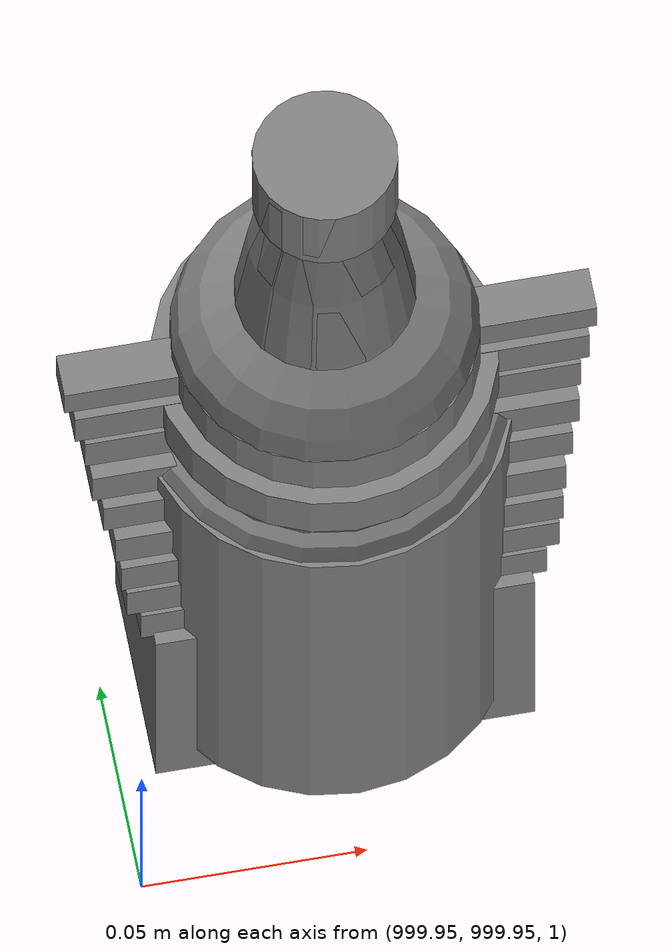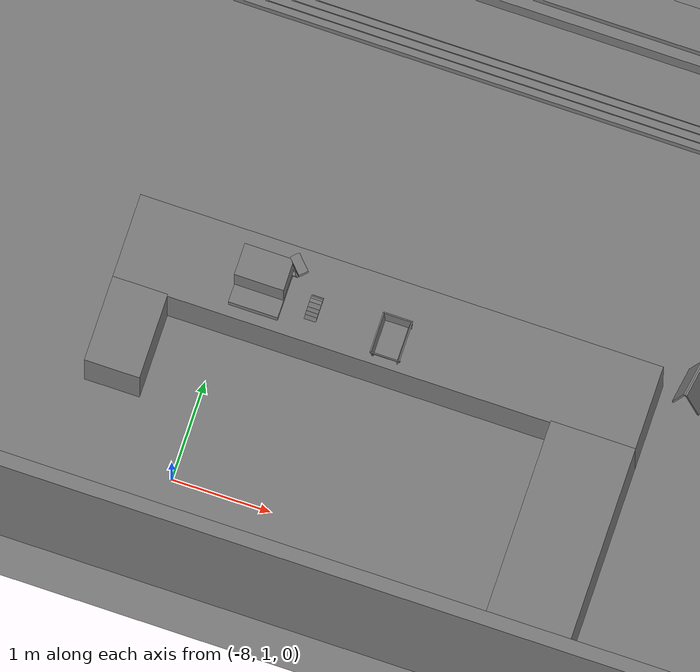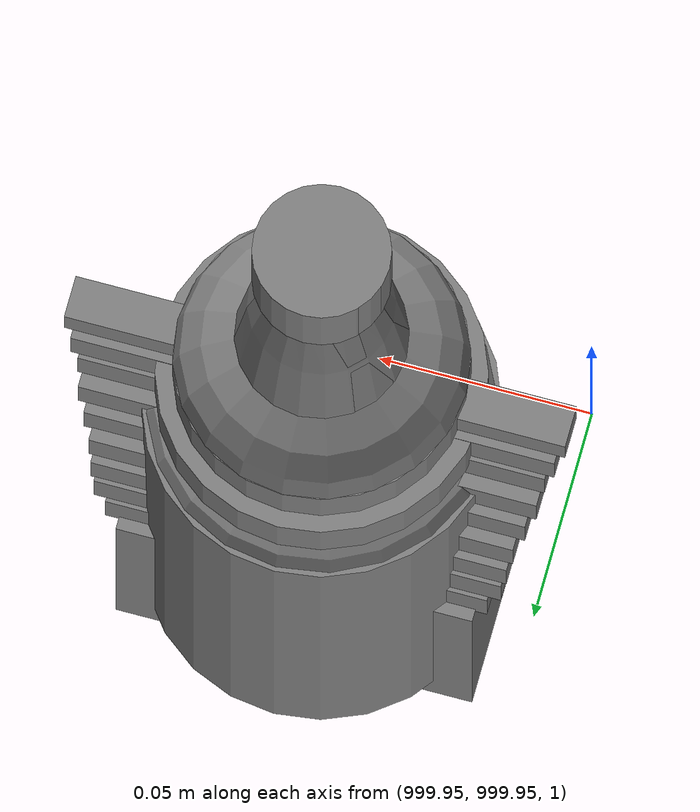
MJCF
<mujoco>
    <option gravity="0.000000000 0.000000000 -9.810000420" timestep="0.0166666" integrator="implicitfast" density="1.225" viscosity="1.8000001e-05" noslip_iterations="10" iterations="100" sdf_iterations="50">
        <flag multiccd="disable"/>
    </option>
    <size memory="1000M"/>
    <compiler coordinate="local"/>
    <worldbody>
        <light cutoff="30" pos="0 1 1" dir="0 -1 -2"/>
        <light cutoff="30" pos="0 -1 1" dir="0 1 -2"/>
        <body pos="-7.168000221 2.823999882 1.227496982" euler="-0.283413976 0.056829724 -0.133293271" name="openloong_gripper_2f85_fix_base_usda_Pos">
            <geom contype="1" conaffinity="1" density="1000" type="box" material="" rgba="0.500000000 0.500000000 0.500000000 1.000000000" solimp="0.899999976 0.949999988 0.001000000" friction="1.000000000 0.005000000 0.000100000" solref="0.020000000 1.000000000" margin="0" condim="3" group="0" pos="-0.002278805 0.074524641 -0.004134059" quat="0.315989345 0.948763072 -0.000000000 0.000000000" size="0.059999999 0.013000000 0.035000000" name="openloong_gripper_2f85_fix_base_usda_geom_0826AE73_4D88_4AA6_B08B_1CC517BB7CB5"/>
            <geom contype="1" conaffinity="1" density="1000" type="box" material="" rgba="0.500000000 0.500000000 0.500000000 1.000000000" solimp="0.899999976 0.949999988 0.001000000" friction="1.000000000 0.005000000 0.000100000" solref="0.020000000 1.000000000" margin="0" condim="3" group="0" pos="-0.002278805 0.078031301 0.008128285" quat="0.990447521 -0.137893379 -0.000000000 -0.000000000" size="0.059999999 0.010000000 0.035000000" name="openloong_gripper_2f85_fix_base_usda_geom_A107544A_E51A_4BC3_B2FF_2B8A477803B6"/>
            <geom contype="1" conaffinity="1" density="1000" type="box" material="" rgba="0.500000000 0.500000000 0.500000000 1.000000000" solimp="0.899999976 0.949999988 0.001000000" friction="1.000000000 0.005000000 0.000100000" solref="0.020000000 1.000000000" margin="0" condim="3" group="0" pos="-0.002278805 0.080785275 -0.002596974" quat="0.287325472 -0.957833409 0.000000000 -0.000000000" size="0.059999999 0.013000000 0.035000000" name="openloong_gripper_2f85_fix_base_usda_geom_FEF9563E_17AF_448A_8C93_3E79217DDAD8"/>
            <geom contype="1" conaffinity="1" density="1000" type="box" material="" rgba="0.500000000 0.500000000 0.500000000 1.000000000" solimp="0.899999976 0.949999988 0.001000000" friction="1.000000000 0.005000000 0.000100000" solref="0.020000000 1.000000000" margin="0" condim="3" group="0" pos="-0.002278805 -0.098804474 -0.020146966" quat="0.988851666 0.148906454 0.000000000 -0.000000000" size="0.059999999 0.022000000 0.020000000" name="openloong_gripper_2f85_fix_base_usda_geom_9E9056DB_13E5_4724_BD8D_AA4028011352"/>
            <geom contype="1" conaffinity="1" density="1000" type="box" material="" rgba="0.500000000 0.500000000 0.500000000 1.000000000" solimp="0.899999976 0.949999988 0.001000000" friction="1.000000000 0.005000000 0.000100000" solref="0.020000000 1.000000000" margin="0" condim="3" group="0" pos="-0.002279282 0.019920111 0.012102962" quat="0.995421767 0.095583342 -0.000000000 -0.000000000" size="0.059999999 0.025000000 0.026000001" name="openloong_gripper_2f85_fix_base_usda_geom_E8CDEB9F_CEE6_49BD_A304_B15B6EFFCAD7"/>
            <geom contype="1" conaffinity="1" density="1000" type="box" material="" rgba="0.500000000 0.500000000 0.500000000 1.000000000" solimp="0.899999976 0.949999988 0.001000000" friction="1.000000000 0.005000000 0.000100000" solref="0.020000000 1.000000000" margin="0" condim="3" group="0" pos="-0.002279282 0.005734444 -0.014276862" quat="0.999571741 -0.029275302 -0.000000000 -0.000000000" size="0.059999999 0.050000001 0.010000000" name="openloong_gripper_2f85_fix_base_usda_geom_BEBC7DA4_2D79_4798_8C90_51D656F62384"/>
            <geom contype="1" conaffinity="1" density="1000" type="box" material="" rgba="0.500000000 0.500000000 0.500000000 1.000000000" solimp="0.899999976 0.949999988 0.001000000" friction="1.000000000 0.005000000 0.000100000" solref="0.020000000 1.000000000" margin="0" condim="3" group="0" pos="-0.002278805 0.079460382 0.007771969" quat="0.922590554 -0.385781586 0.000000000 -0.000000000" size="0.059999999 0.010000000 0.035000000" name="openloong_gripper_2f85_fix_base_usda_geom_2CBB26FA_4AD1_485F_903E_9F8346A539F9"/>
            <geom contype="1" conaffinity="1" density="1000" type="box" material="" rgba="0.500000000 0.500000000 0.500000000 1.000000000" solimp="0.899999976 0.949999988 0.001000000" friction="1.000000000 0.005000000 0.000100000" solref="0.020000000 1.000000000" margin="0" condim="3" group="0" pos="-0.002279282 0.081384182 -0.001320124" quat="0.590483785 -0.807049930 0.000000000 -0.000000000" size="0.059999999 0.013000000 0.035000000" name="openloong_gripper_2f85_fix_base_usda_geom_2FC583CB_2350_4613_963B_6FF64BDB9941"/>
            <geom contype="1" conaffinity="1" density="1000" type="box" material="" rgba="0.500000000 0.500000000 0.500000000 1.000000000" solimp="0.899999976 0.949999988 0.001000000" friction="1.000000000 0.005000000 0.000100000" solref="0.020000000 1.000000000" margin="0" condim="3" group="0" pos="-0.002278805 -0.059297800 -0.007972836" quat="0.988851666 0.148906454 0.000000000 -0.000000000" size="0.059999999 0.020000000 0.022000000" name="openloong_gripper_2f85_fix_base_usda_geom_BA389130_74B2_4C8E_B161_3C261B6AB4FA"/>
            <geom contype="1" conaffinity="1" density="1000" type="box" material="" rgba="0.500000000 0.500000000 0.500000000 1.000000000" solimp="0.899999976 0.949999988 0.001000000" friction="1.000000000 0.005000000 0.000100000" solref="0.020000000 1.000000000" margin="0" condim="3" group="0" pos="-0.002278805 0.076618671 -0.004656792" quat="0.004634961 0.999989629 -0.000000000 0.000000000" size="0.059999999 0.013000000 0.035000000" name="openloong_gripper_2f85_fix_base_usda_geom_1D1802D2_DB6F_4197_B5F3_3FA834C2369F"/>
            <geom contype="1" conaffinity="1" density="1000" type="box" material="" rgba="0.500000000 0.500000000 0.500000000 1.000000000" solimp="0.899999976 0.949999988 0.001000000" friction="1.000000000 0.005000000 0.000100000" solref="0.020000000 1.000000000" margin="0" condim="3" group="0" pos="-0.002279282 -0.021952629 0.002960086" quat="0.991270423 0.131847665 -0.000000000 0.000000000" size="0.059999999 0.020000000 0.024000000" name="openloong_gripper_2f85_fix_base_usda_geom_21728083_AD68_47B9_A397_854F17534731"/>
            <geom contype="1" conaffinity="1" density="1000" type="box" material="" rgba="0.500000000 0.500000000 0.500000000 1.000000000" solimp="0.899999976 0.949999988 0.001000000" friction="1.000000000 0.005000000 0.000100000" solref="0.020000000 1.000000000" margin="0" condim="3" group="0" pos="-0.002278805 0.081418991 0.002587914" quat="0.803492308 -0.595315695 0.000000000 -0.000000000" size="0.059999999 0.013000000 0.035000000" name="openloong_gripper_2f85_fix_base_usda_geom_E88C2A05_8FBC_46C5_9A30_F1CA6FED6850"/>
            <geom contype="1" conaffinity="1" density="1000" type="box" material="" rgba="0.500000000 0.500000000 0.500000000 1.000000000" solimp="0.899999976 0.949999988 0.001000000" friction="1.000000000 0.005000000 0.000100000" solref="0.020000000 1.000000000" margin="0" condim="3" group="0" pos="-0.002278805 0.061115503 0.008545756" quat="0.999326169 0.036714450 0.000000000 -0.000000000" size="0.059999999 0.020000000 0.035000000" name="openloong_gripper_2f85_fix_base_usda_geom_AF257DE9_C288_4958_A4A8_27E9C82E6449"/>
            <freejoint name="openloong_gripper_2f85_fix_base_usda_pos_scan"/>
        </body>
        <body pos="-2.436573029 6.404376507 0.137849092" euler="0.000000000 0.000000000 0.000000000" name="openloong_gripper_2f85_fix_base_usda_shoppingtrolley_01">
            <geom contype="1" conaffinity="1" density="1000" type="box" material="" rgba="0.500000000 0.500000000 0.500000000 1.000000000" solimp="0.899999976 0.949999988 0.001000000" friction="1.000000000 0.005000000 0.000100000" solref="0.020000000 1.000000000" margin="0" condim="3" group="0" pos="-0.169898406 -0.178061336 0.864131629" quat="0.916343808 -0.400392294 -0.000000045 0.000000030" size="0.017999999 0.022499999 0.089999996" name="openloong_gripper_2f85_fix_base_usda_geom_40DD3BDA_E544_4F8E_B520_BD7A7EE745AB"/>
            <geom contype="1" conaffinity="1" density="1000" type="box" material="" rgba="0.500000000 0.500000000 0.500000000 1.000000000" solimp="0.899999976 0.949999988 0.001000000" friction="1.000000000 0.005000000 0.000100000" solref="0.020000000 1.000000000" margin="0" condim="3" group="0" pos="-0.107458733 0.238907143 0.911498845" quat="0.634576976 0.622505128 -0.330067992 -0.317575932" size="0.017999999 0.022499999 0.035999998" name="openloong_gripper_2f85_fix_base_usda_geom_B9160AB3_0E4B_4A36_A622_39AF29EF0B7A"/>
            <geom contype="1" conaffinity="1" density="1000" type="box" material="" rgba="0.500000000 0.500000000 0.500000000 1.000000000" solimp="0.899999976 0.949999988 0.001000000" friction="1.000000000 0.005000000 0.000100000" solref="0.020000000 1.000000000" margin="0" condim="3" group="0" pos="-0.005004787 0.248085022 0.912686050" quat="1.000000000 0.000000000 0.000000000 0.000000000" size="0.107999995 0.022499999 0.022499999" name="openloong_gripper_2f85_fix_base_usda_geom_00FF059B_D9B5_4165_9B2C_60526465BAF5"/>
            <geom contype="1" conaffinity="1" density="1000" type="box" material="" rgba="0.500000000 0.500000000 0.500000000 1.000000000" solimp="0.899999976 0.949999988 0.001000000" friction="1.000000000 0.005000000 0.000100000" solref="0.020000000 1.000000000" margin="0" condim="3" group="0" pos="0.131482959 -0.182533979 0.598989725" quat="0.996607125 0.055331629 0.059003670 0.015205893" size="0.013499999 0.287999988 0.053999998" name="openloong_gripper_2f85_fix_base_usda_geom_763E0986_59E9_4F24_8B72_E287A5FF9917"/>
            <geom contype="1" conaffinity="1" density="1000" type="box" material="" rgba="0.500000000 0.500000000 0.500000000 1.000000000" solimp="0.899999976 0.949999988 0.001000000" friction="1.000000000 0.005000000 0.000100000" solref="0.020000000 1.000000000" margin="0" condim="3" group="0" pos="-0.000005364 0.100332208 0.734785020" quat="0.999668717 0.025737956 -0.000000010 0.000000000" size="0.135000005 0.019800000 0.152999997" name="openloong_gripper_2f85_fix_base_usda_geom_59E25D9C_853D_4B19_B7C2_39D0D6CB6F33"/>
            <geom contype="1" conaffinity="1" density="1000" type="box" material="" rgba="0.500000000 0.500000000 0.500000000 1.000000000" solimp="0.899999976 0.949999988 0.001000000" friction="1.000000000 0.005000000 0.000100000" solref="0.020000000 1.000000000" margin="0" condim="3" group="0" pos="-0.126757339 -0.182533979 0.598989725" quat="0.996607184 0.055331606 -0.059003651 -0.015205891" size="0.013499999 0.287999988 0.053999998" name="openloong_gripper_2f85_fix_base_usda_geom_44B4681E_91BA_441F_BCB9_BA2C1210BBC9"/>
            <geom contype="1" conaffinity="1" density="1000" type="box" material="" rgba="0.500000000 0.500000000 0.500000000 1.000000000" solimp="0.899999976 0.949999988 0.001000000" friction="1.000000000 0.005000000 0.000100000" solref="0.020000000 1.000000000" margin="0" condim="3" group="0" pos="-0.134013891 0.200098798 0.912192523" quat="0.694057047 0.679413557 -0.172947660 -0.163618833" size="0.017999999 0.022499999 0.035999998" name="openloong_gripper_2f85_fix_base_usda_geom_B7633B91_E458_46EE_B439_4FDA3393B648"/>
            <geom contype="1" conaffinity="1" density="1000" type="box" material="" rgba="0.500000000 0.500000000 0.500000000 1.000000000" solimp="0.899999976 0.949999988 0.001000000" friction="1.000000000 0.005000000 0.000100000" solref="0.020000000 1.000000000" margin="0" condim="3" group="0" pos="0.141839072 -0.191051379 0.702451229" quat="0.997147262 0.056065105 0.045779929 0.021407485" size="0.013499999 0.287999988 0.053999998" name="openloong_gripper_2f85_fix_base_usda_geom_F986CD48_939C_4C4D_AD63_351DF03BA135"/>
            <geom contype="1" conaffinity="1" density="1000" type="box" material="" rgba="0.500000000 0.500000000 0.500000000 1.000000000" solimp="0.899999976 0.949999988 0.001000000" friction="1.000000000 0.005000000 0.000100000" solref="0.020000000 1.000000000" margin="0" condim="3" group="0" pos="-0.135714188 -0.191051379 0.694841146" quat="0.997147322 0.056064609 -0.045779683 -0.021407485" size="0.013499999 0.287999988 0.053999998" name="openloong_gripper_2f85_fix_base_usda_geom_9CA78B96_48EC_4D42_8129_CB5D22893D47"/>
            <geom contype="1" conaffinity="1" density="1000" type="box" material="" rgba="0.500000000 0.500000000 0.500000000 1.000000000" solimp="0.899999976 0.949999988 0.001000000" friction="1.000000000 0.005000000 0.000100000" solref="0.020000000 1.000000000" margin="0" condim="3" group="0" pos="-0.000004721 -0.174527690 0.560063601" quat="0.996704638 0.081116498 -0.000000004 0.000000000" size="0.126000002 0.287999988 0.009000000" name="openloong_gripper_2f85_fix_base_usda_geom_8238AB37_B771_471E_AB70_F777591D044F"/>
            <geom contype="1" conaffinity="1" density="1000" type="box" material="" rgba="0.500000000 0.500000000 0.500000000 1.000000000" solimp="0.899999976 0.949999988 0.001000000" friction="1.000000000 0.005000000 0.000100000" solref="0.020000000 1.000000000" margin="0" condim="3" group="0" pos="0.134013891 0.200098798 0.912192523" quat="0.692574680 -0.680924535 -0.166899428 0.169783980" size="0.017999999 0.022499999 0.035999998" name="openloong_gripper_2f85_fix_base_usda_geom_5741AC66_AA71_47D9_9175_1028F316DFB7"/>
            <geom contype="1" conaffinity="1" density="1000" type="box" material="" rgba="0.500000000 0.500000000 0.500000000 1.000000000" solimp="0.899999976 0.949999988 0.001000000" friction="1.000000000 0.005000000 0.000100000" solref="0.020000000 1.000000000" margin="0" condim="3" group="0" pos="-0.012634277 -0.174527690 -0.088243507" quat="1.000000000 0.000000000 -0.000000004 0.000000000" size="0.135000005 0.287999988 0.044999998" name="openloong_gripper_2f85_fix_base_usda_geom_E8820B23_430F_42DE_9BBA_EF0D903CC285"/>
            <geom contype="1" conaffinity="1" density="1000" type="box" material="" rgba="0.500000000 0.500000000 0.500000000 1.000000000" solimp="0.899999976 0.949999988 0.001000000" friction="1.000000000 0.005000000 0.000100000" solref="0.020000000 1.000000000" margin="0" condim="3" group="0" pos="-0.142927840 -0.199506134 0.784674108" quat="0.998421252 0.016904408 -0.027109101 -0.046199299" size="0.013499999 0.305999994 0.063000001" name="openloong_gripper_2f85_fix_base_usda_geom_E6082A6B_0A37_461E_93CE_DF0ABD73C3F7"/>
            <geom contype="1" conaffinity="1" density="1000" type="box" material="" rgba="0.500000000 0.500000000 0.500000000 1.000000000" solimp="0.899999976 0.949999988 0.001000000" friction="1.000000000 0.005000000 0.000100000" solref="0.020000000 1.000000000" margin="0" condim="3" group="0" pos="-0.169898406 -0.043119621 0.915120542" quat="0.687021017 0.726584017 -0.005590606 -0.006832919" size="0.017999999 0.022499999 0.089999996" name="openloong_gripper_2f85_fix_base_usda_geom_60688D13_B32B_4FDE_BFA4_4869F2591AF9"/>
            <geom contype="1" conaffinity="1" density="1000" type="box" material="" rgba="0.500000000 0.500000000 0.500000000 1.000000000" solimp="0.899999976 0.949999988 0.001000000" friction="1.000000000 0.005000000 0.000100000" solref="0.020000000 1.000000000" margin="0" condim="3" group="0" pos="-0.000006008 -0.484932661 0.670727849" quat="0.997585475 0.069449045 -0.000000004 -0.000000089" size="0.179999992 0.013499999 0.170999989" name="openloong_gripper_2f85_fix_base_usda_geom_06C4C135_54BB_447C_A138_E56EC223443D"/>
            <geom contype="1" conaffinity="1" density="1000" type="box" material="" rgba="0.500000000 0.500000000 0.500000000 1.000000000" solimp="0.899999976 0.949999988 0.001000000" friction="1.000000000 0.005000000 0.000100000" solref="0.020000000 1.000000000" margin="0" condim="3" group="0" pos="0.160832971 0.103427693 0.910528183" quat="0.711112797 -0.700149298 -0.042821646 0.047705106" size="0.017999999 0.022499999 0.071999997" name="openloong_gripper_2f85_fix_base_usda_geom_419EE062_5739_42A6_8F5F_B62536933D6B"/>
            <geom contype="1" conaffinity="1" density="1000" type="box" material="" rgba="0.500000000 0.500000000 0.500000000 1.000000000" solimp="0.899999976 0.949999988 0.001000000" friction="1.000000000 0.005000000 0.000100000" solref="0.020000000 1.000000000" margin="0" condim="3" group="0" pos="-0.160832763 0.103427693 0.910528183" quat="0.711469591 0.699786782 -0.048386075 -0.042050660" size="0.017999999 0.022499999 0.071999997" name="openloong_gripper_2f85_fix_base_usda_geom_3DC2666A_96BD_4761_98AB_62AE70AE0B0B"/>
            <geom contype="1" conaffinity="1" density="1000" type="box" material="" rgba="0.500000000 0.500000000 0.500000000 1.000000000" solimp="0.899999976 0.949999988 0.001000000" friction="1.000000000 0.005000000 0.000100000" solref="0.020000000 1.000000000" margin="0" condim="3" group="0" pos="0.169898629 -0.178061336 0.864131629" quat="0.916343808 -0.400392294 -0.000000045 0.000000030" size="0.017999999 0.022499999 0.089999996" name="openloong_gripper_2f85_fix_base_usda_geom_AC3B2C1E_0BD2_471C_9F4B_3A99F92198F5"/>
            <geom contype="1" conaffinity="1" density="1000" type="box" material="" rgba="0.500000000 0.500000000 0.500000000 1.000000000" solimp="0.899999976 0.949999988 0.001000000" friction="1.000000000 0.005000000 0.000100000" solref="0.020000000 1.000000000" margin="0" condim="3" group="0" pos="0.103667587 0.233050480 0.912927270" quat="0.634205043 -0.622199059 -0.324503720 0.324576139" size="0.017999999 0.022499999 0.035999998" name="openloong_gripper_2f85_fix_base_usda_geom_BEB52E09_651A_4133_BF1D_416B6FD3385D"/>
            <geom contype="1" conaffinity="1" density="1000" type="box" material="" rgba="0.500000000 0.500000000 0.500000000 1.000000000" solimp="0.899999976 0.949999988 0.001000000" friction="1.000000000 0.005000000 0.000100000" solref="0.020000000 1.000000000" margin="0" condim="3" group="0" pos="0.169898629 -0.043119621 0.915120542" quat="0.687029123 -0.726576388 -0.006509603 0.005963952" size="0.017999999 0.022499999 0.089999996" name="openloong_gripper_2f85_fix_base_usda_geom_8D7985B8_27A7_4FBC_8D5B_5FA9FB2EA947"/>
            <geom contype="1" conaffinity="1" density="1000" type="box" material="" rgba="0.500000000 0.500000000 0.500000000 1.000000000" solimp="0.899999976 0.949999988 0.001000000" friction="1.000000000 0.005000000 0.000100000" solref="0.020000000 1.000000000" margin="0" condim="3" group="0" pos="0.148195267 -0.199506566 0.782808602" quat="0.998808920 0.017156634 0.026950166 0.036880098" size="0.013499999 0.305999994 0.063000001" name="openloong_gripper_2f85_fix_base_usda_geom_E6E12E14_A41A_4243_A251_985BB4FBB8E2"/>
            <freejoint name="openloong_gripper_2f85_fix_base_usda_shoppingtrolley_01_joint"/>
            <site size="0.005000000 0.005000000 0.005000000" rgba="0.500000000 0.500000000 0.500000000 1.000000000" pos="0.000000000 0.000000000 0.000000000" quat="1.000000000 0.000000000 0.000000000 0.000000000" group="0" type="sphere" name="openloong_gripper_2f85_fix_base_usda_shoppingtrolley_01"/>
        </body>
        <body pos="-6.332345009 2.779978037 1.034067392" euler="0.000000000 0.000000000 0.000000000" name="openloong_gripper_2f85_fix_base_usda_basket">
            <geom contype="1" conaffinity="1" density="100000" type="box" material="" rgba="0.500000000 0.500000000 0.500000000 1.000000000" solimp="0.899999976 0.949999988 0.001000000" friction="1.000000000 0.899999976 0.000100000" solref="0.020000000 1.000000000" margin="0" condim="3" group="0" pos="-0.172339439 0.000000000 0.168361664" quat="0.706172407 -0.036353018 -0.036353093 0.706170976" size="0.200000003 0.006000000 0.108000003" name="openloong_gripper_2f85_fix_base_usda_geom_AA55D347_9AF3_4AAA_BFFA_47B697BC99A3"/>
            <geom contype="1" conaffinity="1" density="100000" type="box" material="" rgba="0.500000000 0.500000000 0.500000000 1.000000000" solimp="0.899999976 0.949999988 0.001000000" friction="1.000000000 0.899999976 0.000100000" solref="0.020000000 1.000000000" margin="0" condim="3" group="0" pos="-0.039724827 -0.188568115 0.167089701" quat="0.997537494 0.070135131 0.000000000 0.000000000" size="0.150000006 0.006000000 0.108000003" name="openloong_gripper_2f85_fix_base_usda_geom_EE6FD328_31E6_4FB0_A90D_271756AAD474"/>
            <geom contype="1" conaffinity="1" density="100000" type="box" material="" rgba="0.500000000 0.500000000 0.500000000 1.000000000" solimp="0.899999976 0.949999988 0.001000000" friction="1.000000000 0.899999976 0.000100000" solref="0.020000000 1.000000000" margin="0" condim="3" group="0" pos="-0.039724827 0.188377380 0.167089701" quat="0.997489929 -0.070808925 0.000000000 0.000000000" size="0.150000006 0.006000000 0.108000003" name="openloong_gripper_2f85_fix_base_usda_geom_44C861CD_1AC3_4EA1_8358_09C34DD2B668"/>
            <geom contype="1" conaffinity="1" density="100000" type="box" material="" rgba="0.500000000 0.500000000 0.500000000 1.000000000" solimp="0.899999976 0.949999988 0.001000000" friction="1.000000000 0.899999976 0.000100000" solref="0.020000000 1.000000000" margin="0" condim="3" group="0" pos="-0.039724827 0.000000000 0.068126202" quat="1.000000000 0.000000000 0.000000000 0.000000000" size="0.129999995 0.174999997 0.006000000" name="openloong_gripper_2f85_fix_base_usda_geom_5DB33131_C702_4DD8_87D3_FF298163F41C"/>
            <geom contype="1" conaffinity="1" density="100000" type="box" material="" rgba="0.500000000 0.500000000 0.500000000 1.000000000" solimp="0.899999976 0.949999988 0.001000000" friction="1.000000000 0.899999976 0.000100000" solref="0.020000000 1.000000000" margin="0" condim="3" group="0" pos="0.094372749 0.000000000 0.168361664" quat="0.706172049 0.036353335 0.036353379 0.706171215" size="0.200000003 0.006000000 0.108000003" name="openloong_gripper_2f85_fix_base_usda_geom_7173EA1E_29C1_4A73_B658_B8E2DC979838"/>
            <freejoint name="openloong_gripper_2f85_fix_base_usda_basket_joint"/>
            <site size="0.005000000 0.005000000 0.005000000" rgba="0.500000000 0.500000000 0.500000000 1.000000000" pos="0.000000000 0.000000000 0.000000000" quat="1.000000000 0.000000000 0.000000000 0.000000000" group="0" type="sphere" name="openloong_gripper_2f85_fix_base_usda_basketsite"/>
        </body>
        <body pos="-3.510578632 3.403555870 -0.000000100" euler="0.000000000 0.000000000 40.200675964" name="openloong_gripper_2f85_fix_base_usda_PZ">
            <geom contype="1" conaffinity="1" density="1000" type="box" material="" rgba="0.500000000 0.500000000 0.500000000 1.000000000" solimp="0.899999976 0.949999988 0.001000000" friction="1.000000000 0.005000000 0.000100000" solref="0.020000000 1.000000000" margin="0" condim="3" group="0" pos="-0.047453165 0.056484699 0.373715430" quat="0.934750080 0.077914521 0.028795123 0.345459938" size="0.180000007 0.010000000 0.379999995" name="openloong_gripper_2f85_fix_base_usda_geom_4195563C_185B_4888_845C_260C9027BF59"/>
            <geom contype="1" conaffinity="1" density="1000" type="box" material="" rgba="0.500000000 0.500000000 0.500000000 1.000000000" solimp="0.899999976 0.949999988 0.001000000" friction="1.000000000 0.005000000 0.000100000" solref="0.020000000 1.000000000" margin="0" condim="3" group="0" pos="0.047452450 -0.054376602 0.374072611" quat="0.934387863 -0.082143910 -0.030358355 0.345326364" size="0.180000007 0.010000000 0.379999995" name="openloong_gripper_2f85_fix_base_usda_geom_17404A05_8899_4492_BB31_E35421159F0F"/>
            <freejoint name="openloong_gripper_2f85_fix_base_usda_PZ"/>
        </body>
        <body pos="0.000000000 0.000000000 0.000000000" euler="0.000000000 0.000000000 0.000000000" name=" Static Objects_ Static Objects">
            <geom contype="1" conaffinity="1" density="1000" type="box" material="" rgba="0.500000000 0.500000000 0.500000000 1.000000000" solimp="0.899999976 0.949999988 0.001000000" friction="1.000000000 0.005000000 0.000100000" solref="0.020000000 1.000000000" margin="0" condim="3" group="0" pos="-3.101639986 6.150595188 1.018643856" quat="1.000000000 0.000000000 0.000000000 0.000000000" size="0.050000001 0.579999983 1.019999981" name=" Static Objects_geom_5C37F840_8F1F_47C8_9048_56029C5309EB"/>
            <geom contype="1" conaffinity="1" density="1000" type="box" material="" rgba="0.500000000 0.500000000 0.500000000 1.000000000" solimp="0.899999976 0.949999988 0.001000000" friction="1.000000000 0.005000000 0.000100000" solref="0.020000000 1.000000000" margin="0" condim="3" group="0" pos="-2.825197220 6.153595448 1.115278244" quat="0.707107067 0.000000000 0.000000000 0.707106471" size="0.550000012 0.239999995 0.025000000" name=" Static Objects_geom_36132E83_8395_4B9D_8352_2136C00E0F18"/>
            <geom contype="1" conaffinity="1" density="1000" type="box" material="" rgba="0.500000000 0.500000000 0.500000000 1.000000000" solimp="0.899999976 0.949999988 0.001000000" friction="1.000000000 0.005000000 0.000100000" solref="0.020000000 1.000000000" margin="0" condim="3" group="0" pos="-2.825197220 6.153595448 0.097434282" quat="0.707107067 0.000000000 0.000000000 0.707106471" size="0.550000012 0.239999995 0.098999999" name=" Static Objects_geom_57C01D87_5620_4854_A557_D8D341567EB3"/>
            <geom contype="1" conaffinity="1" density="1000" type="box" material="" rgba="0.500000000 0.500000000 0.500000000 1.000000000" solimp="0.899999976 0.949999988 0.001000000" friction="1.000000000 0.005000000 0.000100000" solref="0.020000000 1.000000000" margin="0" condim="3" group="0" pos="-6.293097973 6.153595448 1.114443064" quat="0.707107067 0.000000000 0.000000000 0.707106471" size="0.529999971 3.134999990 0.025000000" name=" Static Objects_geom_5203BE54_AC36_4349_AC96_3000134B458C"/>
            <geom contype="1" conaffinity="1" density="1000" type="box" material="" rgba="0.500000000 0.500000000 0.500000000 1.000000000" solimp="0.899999976 0.949999988 0.001000000" friction="1.000000000 0.005000000 0.000100000" solref="0.020000000 1.000000000" margin="0" condim="3" group="0" pos="-6.286010742 6.153595448 0.096129179" quat="0.707107067 0.000000000 0.000000000 0.707106471" size="0.529999971 3.134999990 0.098999999" name=" Static Objects_geom_60F512B0_810F_4D7C_A431_930E7B846FD0"/>
            <geom contype="1" conaffinity="1" density="1000" type="box" material="" rgba="0.500000000 0.500000000 0.500000000 1.000000000" solimp="0.899999976 0.949999988 0.001000000" friction="1.000000000 0.005000000 0.000100000" solref="0.020000000 1.000000000" margin="0" condim="3" group="0" pos="-2.825197220 6.153595448 1.563861728" quat="0.707107067 0.000000000 0.000000000 0.707106471" size="0.550000012 0.239999995 0.025000000" name=" Static Objects_geom_2D6C1B0C_97E2_4CF7_B90E_BAEC31B143D8"/>
            <geom contype="1" conaffinity="1" density="1000" type="box" material="" rgba="0.500000000 0.500000000 0.500000000 1.000000000" solimp="0.899999976 0.949999988 0.001000000" friction="1.000000000 0.005000000 0.000100000" solref="0.020000000 1.000000000" margin="0" condim="3" group="0" pos="-6.311686516 6.153595448 1.018643856" quat="0.707107067 0.000000000 0.000000000 0.707106471" size="0.050000001 3.150000095 1.019999981" name=" Static Objects_geom_4386AA14_34E5_403E_ADA1_5EB3629EF0FB"/>
            <geom contype="1" conaffinity="1" density="1000" type="box" material="" rgba="0.500000000 0.500000000 0.500000000 1.000000000" solimp="0.899999976 0.949999988 0.001000000" friction="1.000000000 0.005000000 0.000100000" solref="0.020000000 1.000000000" margin="0" condim="3" group="0" pos="-2.825197220 6.153595448 0.629031777" quat="0.707107067 0.000000000 0.000000000 0.707106471" size="0.550000012 0.239999995 0.025000000" name=" Static Objects_geom_EC3EDAA2_CB7F_4995_8A1C_82AAFEF89CF4"/>
            <geom contype="1" conaffinity="1" density="1000" type="box" material="" rgba="0.500000000 0.500000000 0.500000000 1.000000000" solimp="0.899999976 0.949999988 0.001000000" friction="1.000000000 0.005000000 0.000100000" solref="0.020000000 1.000000000" margin="0" condim="3" group="0" pos="-6.286010742 6.153595448 1.563861728" quat="0.707107067 0.000000000 0.000000000 0.707106471" size="0.529999971 3.134999990 0.025000000" name=" Static Objects_geom_9EB34E1E_4263_41D9_AB15_68CA0C79B16E"/>
            <geom contype="1" conaffinity="1" density="1000" type="box" material="" rgba="0.500000000 0.500000000 0.500000000 1.000000000" solimp="0.899999976 0.949999988 0.001000000" friction="1.000000000 0.005000000 0.000100000" solref="0.020000000 1.000000000" margin="0" condim="3" group="0" pos="-6.286010742 6.153595448 0.629031777" quat="0.707107067 0.000000000 0.000000000 0.707106471" size="0.529999971 3.134999990 0.025000000" name=" Static Objects_geom_6761193E_1B04_4106_AE45_0E3100425B92"/>
            <geom contype="1" conaffinity="1" density="1000" type="box" material="" rgba="0.500000000 0.500000000 0.500000000 1.000000000" solimp="0.899999976 0.949999988 0.001000000" friction="1.000000000 0.005000000 0.000100000" solref="0.020000000 1.000000000" margin="0" condim="3" group="0" pos="-7.719123363 2.867671013 1.173410416" quat="1.000000000 0.000000000 0.000000000 0.000000000" size="0.250000000 0.250000000 0.079999998" name=" Static Objects_geom_33E9B8A2_5BBA_4883_AFB1_30480D2521DA"/>
            <geom contype="1" conaffinity="1" density="1000" type="box" material="" rgba="0.500000000 0.500000000 0.500000000 1.000000000" solimp="0.899999976 0.949999988 0.001000000" friction="1.000000000 0.005000000 0.000100000" solref="0.020000000 1.000000000" margin="0" condim="3" group="0" pos="-7.408766270 3.088089943 1.776644945" quat="0.928051054 0.000000000 0.000000000 0.372453064" size="0.050000001 0.100000001 0.050000001" name=" Static Objects_geom_DFF5FC1F_6FDE_4B69_97C4_C51FEF5BA1AE"/>
            <geom contype="1" conaffinity="1" density="1000" type="box" material="" rgba="0.500000000 0.500000000 0.500000000 1.000000000" solimp="0.899999976 0.949999988 0.001000000" friction="1.000000000 0.005000000 0.000100000" solref="0.020000000 1.000000000" margin="0" condim="3" group="0" pos="-7.719123363 2.958004713 1.530241251" quat="1.000000000 0.000000000 0.000000000 0.000000000" size="0.250000000 0.159999996 0.280000001" name=" Static Objects_geom_7993FF12_7AC6_4D69_9EC3_D35427E0D973"/>
            <geom contype="1" conaffinity="1" density="1000" type="cylinder" material="" rgba="0.500000000 0.500000000 0.500000000 1.000000000" solimp="0.899999976 0.949999988 0.001000000" friction="1.000000000 0.005000000 0.000100000" solref="0.020000000 1.000000000" margin="0" condim="3" group="0" pos="-7.427312374 3.069516420 1.502544641" quat="0.928051054 0.000000000 0.000000000 0.372453064" size="0.015000000 0.230000004 0.100000001" name=" Static Objects_geom_72F5C791_1B58_4967_9A7D_365A64DBB8A8"/>
            <geom contype="1" conaffinity="1" density="1000" type="box" material="" rgba="0.500000000 0.500000000 0.500000000 1.000000000" solimp="0.899999976 0.949999988 0.001000000" friction="1.000000000 0.005000000 0.000100000" solref="0.020000000 1.000000000" margin="0" condim="3" group="0" pos="-7.437745571 3.067511320 1.289965630" quat="1.000000000 0.000000000 0.000000000 0.000000000" size="0.029999999 0.020000000 0.020000000" name=" Static Objects_geom_D2F0504E_C8EA_45C1_A49E_DC4641A2C602"/>
            <geom contype="1" conaffinity="1" density="1000" type="box" material="" rgba="0.500000000 0.500000000 0.500000000 1.000000000" solimp="0.899999976 0.949999988 0.001000000" friction="1.000000000 0.005000000 0.000100000" solref="0.020000000 1.000000000" margin="0" condim="3" group="0" pos="-9.058088303 6.434794426 1.209077358" quat="1.000000000 0.000000000 0.000000000 0.000000000" size="0.250000000 0.100000001 0.070000000" name=" Static Objects_geom_4CB592F0_9E8F_4285_B543_ADA8F612A66C"/>
            <geom contype="1" conaffinity="1" density="1000" type="box" material="" rgba="0.500000000 0.500000000 0.500000000 1.000000000" solimp="0.899999976 0.949999988 0.001000000" friction="1.000000000 0.005000000 0.000100000" solref="0.020000000 1.000000000" margin="0" condim="3" group="0" pos="-7.886891365 6.459744930 0.352518857" quat="1.000000000 0.000000000 0.000000000 0.000000000" size="1.500000000 0.200000003 0.150000006" name=" Static Objects_geom_34BF117A_8EA2_4032_A31B_22E5C2C25A44"/>
            <geom contype="1" conaffinity="1" density="1000" type="box" material="" rgba="0.500000000 0.500000000 0.500000000 1.000000000" solimp="0.899999976 0.949999988 0.001000000" friction="1.000000000 0.005000000 0.000100000" solref="0.020000000 1.000000000" margin="0" condim="3" group="0" pos="-9.237723351 6.464855671 1.209077358" quat="1.000000000 0.000000000 0.000000000 0.000000000" size="0.100000001 0.100000001 0.070000000" name=" Static Objects_geom_DD4525B6_DF46_4857_805D_4BE922E23407"/>
            <geom contype="1" conaffinity="1" density="1000" type="box" material="" rgba="0.500000000 0.500000000 0.500000000 1.000000000" solimp="0.899999976 0.949999988 0.001000000" friction="1.000000000 0.005000000 0.000100000" solref="0.020000000 1.000000000" margin="0" condim="3" group="0" pos="-6.924745083 6.362090111 1.214329123" quat="1.000000000 0.000000000 0.000000000 0.000000000" size="0.200000003 0.100000001 0.075000003" name=" Static Objects_geom_A6DD5715_F77B_4BFF_9354_6B9BF2D20AD4"/>
            <geom contype="1" conaffinity="1" density="1000" type="box" material="" rgba="0.500000000 0.500000000 0.500000000 1.000000000" solimp="0.899999976 0.949999988 0.001000000" friction="1.000000000 0.005000000 0.000100000" solref="0.020000000 1.000000000" margin="0" condim="3" group="0" pos="-4.407354832 6.459744930 1.292199373" quat="1.000000000 0.000000000 0.000000000 0.000000000" size="1.240000010 0.200000003 0.150000006" name=" Static Objects_geom_B673093E_43F8_462B_BBEB_D795EE87798D"/>
            <geom contype="1" conaffinity="1" density="1000" type="box" material="" rgba="0.500000000 0.500000000 0.500000000 1.000000000" solimp="0.899999976 0.949999988 0.001000000" friction="1.000000000 0.005000000 0.000100000" solref="0.020000000 1.000000000" margin="0" condim="3" group="0" pos="-5.611940861 6.318420410 0.350975692" quat="1.000000000 0.000000000 0.000000000 0.000000000" size="0.699999988 0.100000001 0.150000006" name=" Static Objects_geom_B5ED7813_059A_43B4_BEE4_83A9312201AB"/>
            <geom contype="1" conaffinity="1" density="1000" type="box" material="" rgba="0.500000000 0.500000000 0.500000000 1.000000000" solimp="0.899999976 0.949999988 0.001000000" friction="1.000000000 0.005000000 0.000100000" solref="0.020000000 1.000000000" margin="0" condim="3" group="0" pos="-6.300771236 6.459744930 1.744376063" quat="1.000000000 0.000000000 0.000000000 0.000000000" size="3.000000000 0.200000003 0.150000006" name=" Static Objects_geom_E2FA6F17_9BAE_474A_A714_761B9D6628A1"/>
            <geom contype="1" conaffinity="1" density="1000" type="box" material="" rgba="0.500000000 0.500000000 0.500000000 1.000000000" solimp="0.899999976 0.949999988 0.001000000" friction="1.000000000 0.005000000 0.000100000" solref="0.020000000 1.000000000" margin="0" condim="3" group="0" pos="-6.751636982 6.459744930 0.800981164" quat="1.000000000 0.000000000 0.000000000 0.000000000" size="2.200000048 0.200000003 0.150000006" name=" Static Objects_geom_AB1BDEAB_0CA4_4BCF_8480_D698CDEE7646"/>
            <geom contype="1" conaffinity="1" density="1000" type="box" material="" rgba="0.500000000 0.500000000 0.500000000 1.000000000" solimp="0.899999976 0.949999988 0.001000000" friction="1.000000000 0.005000000 0.000100000" solref="0.020000000 1.000000000" margin="0" condim="3" group="0" pos="-8.844120979 6.464855671 1.209077358" quat="1.000000000 0.000000000 0.000000000 0.000000000" size="0.100000001 0.100000001 0.070000000" name=" Static Objects_geom_ED0D141C_D958_4038_A7B2_B68B4C642151"/>
            <geom contype="1" conaffinity="1" density="1000" type="box" material="" rgba="0.500000000 0.500000000 0.500000000 1.000000000" solimp="0.899999976 0.949999988 0.001000000" friction="1.000000000 0.005000000 0.000100000" solref="0.020000000 1.000000000" margin="0" condim="3" group="0" pos="-6.098561764 6.327973843 1.292199373" quat="1.000000000 0.000000000 0.000000000 0.000000000" size="0.500000000 0.100000001 0.150000006" name=" Static Objects_geom_FED05DFB_5162_4CC8_9B76_639C80E8D32C"/>
            <geom contype="1" conaffinity="1" density="1000" type="box" material="" rgba="0.500000000 0.500000000 0.500000000 1.000000000" solimp="0.899999976 0.949999988 0.001000000" friction="1.000000000 0.005000000 0.000100000" solref="0.020000000 1.000000000" margin="0" condim="3" group="0" pos="-6.824534416 6.447464466 1.212718010" quat="1.000000000 0.000000000 0.000000000 0.000000000" size="0.100000001 0.100000001 0.075000003" name=" Static Objects_geom_69787C71_7364_412E_B1D7_564F6D0F3745"/>
            <geom contype="1" conaffinity="1" density="1000" type="box" material="" rgba="0.500000000 0.500000000 0.500000000 1.000000000" solimp="0.899999976 0.949999988 0.001000000" friction="1.000000000 0.005000000 0.000100000" solref="0.020000000 1.000000000" margin="0" condim="3" group="0" pos="-3.907610416 6.318625927 0.800981164" quat="1.000000000 0.000000000 0.000000000 0.000000000" size="0.500000000 0.100000001 0.150000006" name=" Static Objects_geom_789F285C_555B_41F7_9D15_196DCB4C5317"/>
            <geom contype="1" conaffinity="1" density="1000" type="box" material="" rgba="0.500000000 0.500000000 0.500000000 1.000000000" solimp="0.899999976 0.949999988 0.001000000" friction="1.000000000 0.005000000 0.000100000" solref="0.020000000 1.000000000" margin="0" condim="3" group="0" pos="-7.373087406 6.458900928 1.214329123" quat="1.000000000 0.000000000 0.000000000 0.000000000" size="0.250000000 0.200000003 0.075000003" name=" Static Objects_geom_863D0076_EC96_41B6_80E8_615EB1F1D2E6"/>
            <geom contype="1" conaffinity="1" density="1000" type="box" material="" rgba="0.500000000 0.500000000 0.500000000 1.000000000" solimp="0.899999976 0.949999988 0.001000000" friction="1.000000000 0.005000000 0.000100000" solref="0.020000000 1.000000000" margin="0" condim="3" group="0" pos="-4.035642624 6.459744930 0.352518857" quat="1.000000000 0.000000000 0.000000000 0.000000000" size="0.800000012 0.200000003 0.150000006" name=" Static Objects_geom_08463EA7_D1D8_4AD1_8850_F66F627B6C7B"/>
            <geom contype="1" conaffinity="1" density="1000" type="box" material="" rgba="0.500000000 0.500000000 0.500000000 1.000000000" solimp="0.899999976 0.949999988 0.001000000" friction="1.000000000 0.005000000 0.000100000" solref="0.020000000 1.000000000" margin="0" condim="3" group="0" pos="-6.460197449 2.937205315 0.548931718" quat="1.000000000 0.000000000 0.000000000 0.000000000" size="2.650000095 0.430000007 0.550000012" name=" Static Objects_geom_903F5A87_53CD_418A_81B0_F740B9E8895F"/>
            <geom contype="1" conaffinity="1" density="1000" type="box" material="" rgba="0.500000000 0.500000000 0.500000000 1.000000000" solimp="0.899999976 0.949999988 0.001000000" friction="1.000000000 0.005000000 0.000100000" solref="0.020000000 1.000000000" margin="0" condim="3" group="0" pos="-4.240264893 1.327049494 0.549888909" quat="1.000000000 0.000000000 0.000000000 0.000000000" size="0.430000007 1.200000048 0.550000012" name=" Static Objects_geom_3CE82F3D_35FE_4BFA_B632_A45FC2A374F6"/>
            <geom contype="1" conaffinity="1" density="1000" type="box" material="" rgba="0.500000000 0.500000000 0.500000000 1.000000000" solimp="0.899999976 0.949999988 0.001000000" friction="1.000000000 0.005000000 0.000100000" solref="0.020000000 1.000000000" margin="0" condim="3" group="0" pos="-8.830721855 2.096410990 0.549305558" quat="1.000000000 0.000000000 0.000000000 0.000000000" size="0.280000001 0.430000007 0.550000012" name=" Static Objects_geom_1EC06FBD_C7EC_4AC7_A711_E45F81FA318B"/>
            <geom contype="1" conaffinity="1" density="1000" type="plane" material="" rgba="0.500000000 0.500000000 0.500000000 1.000000000" solimp="0.899999976 0.949999988 0.001000000" friction="1.000000000 0.005000000 0.000100000" solref="0.020000000 1.000000000" margin="0" condim="3" group="0" pos="-6.000000000 10.399999619 0.000000000" quat="1.000000000 0.000000000 0.000000000 0.000000000" size="6.050000191 10.800000191 0.010000000" name=" Static Objects_geom_7DF14162_0E0C_48B4_BCEF_EA0EC954D2E3"/>
            <geom contype="1" conaffinity="1" density="1000" type="box" material="" rgba="0.500000000 0.500000000 0.500000000 1.000000000" solimp="0.899999976 0.949999988 0.001000000" friction="1.000000000 0.005000000 0.000100000" solref="0.020000000 1.000000000" margin="0" condim="3" group="0" pos="-6.000000000 0.035000000 2.000000000" quat="1.000000000 0.000000000 0.000000000 0.000000000" size="6.079999924 0.070000000 2.000000000" name=" Static Objects_geom_8785A95F_F7C9_49A4_853E_C78B0FB13C1F"/>
            <geom contype="1" conaffinity="1" density="1000" type="box" material="" rgba="0.500000000 0.500000000 0.500000000 1.000000000" solimp="0.899999976 0.949999988 0.001000000" friction="1.000000000 0.005000000 0.000100000" solref="0.020000000 1.000000000" margin="0" condim="3" group="0" pos="-6.000000000 20.159999847 2.000000000" quat="1.000000000 0.000000000 0.000000000 0.000000000" size="6.079999924 0.070000000 2.000000000" name=" Static Objects_geom_A8C1D1E7_894B_4338_9F6B_F09795D1EE7F"/>
            <geom contype="1" conaffinity="1" density="1000" type="box" material="" rgba="0.500000000 0.500000000 0.500000000 1.000000000" solimp="0.899999976 0.949999988 0.001000000" friction="1.000000000 0.005000000 0.000100000" solref="0.020000000 1.000000000" margin="0" condim="3" group="0" pos="0.000000000 10.000000000 2.000000000" quat="1.000000000 0.000000000 0.000000000 0.000000000" size="0.070000000 10.500000000 2.000000000" name=" Static Objects_geom_33D68942_83BB_4390_860B_1E335BE63950"/>
            <geom contype="1" conaffinity="1" density="1000" type="box" material="" rgba="0.500000000 0.500000000 0.500000000 1.000000000" solimp="0.899999976 0.949999988 0.001000000" friction="1.000000000 0.005000000 0.000100000" solref="0.020000000 1.000000000" margin="0" condim="3" group="0" pos="-12.050000191 10.000000000 2.000000000" quat="1.000000000 0.000000000 0.000000000 0.000000000" size="0.070000000 10.500000000 2.000000000" name=" Static Objects_geom_C82D4AAE_4F5C_49DF_B908_C48B8286A1B7"/>
        </body>
        <body pos="0.000000000 0.000000000 0.000000000" euler="0.000000000 0.000000000 0.000000000" name="Interactive Objects_Interactive Objects"/>
        <body pos="1000.000000000 1000.000000000 1.000000000" euler="0.000000000 0.000000000 0.000000000" name="openloong_gripper_2f85_fix_base_usda_bottle_blue">
            <geom contype="1" conaffinity="1" density="1000" type="ellipsoid" material="" rgba="0.500000000 0.500000000 0.500000000 1.000000000" solimp="0.899999976 0.949999988 0.001000000" friction="1.000000000 0.005000000 0.000100000" solref="0.020000000 1.000000000" margin="0" condim="3" group="0" pos="0.000000000 0.000000000 0.118920922" quat="1.000000000 0.000000000 0.000000000 0.000000000" size="0.030999999 0.030999999 0.029999999" name="openloong_gripper_2f85_fix_base_usda_geom_E860D996_D4E0_42FB_92FA_EDC59E5343DC"/>
            <geom contype="1" conaffinity="1" density="1000" type="box" material="" rgba="0.500000000 0.500000000 0.500000000 1.000000000" solimp="0.899999976 0.949999988 0.001000000" friction="1.000000000 0.005000000 0.000100000" solref="0.020000000 1.000000000" margin="0" condim="3" group="0" pos="0.000000000 0.000000000 0.002164602" quat="1.000000000 0.000000000 0.000000000 0.000000000" size="0.020000000 0.020000000 0.003000000" name="openloong_gripper_2f85_fix_base_usda_geom_64CCFD30_ACDF_4058_95C0_2541DDE01CE5"/>
            <geom contype="1" conaffinity="1" density="1000" type="cylinder" material="" rgba="0.500000000 0.500000000 0.500000000 1.000000000" solimp="0.899999976 0.949999988 0.001000000" friction="1.000000000 0.005000000 0.000100000" solref="0.020000000 1.000000000" margin="0" condim="3" group="0" pos="0.000000000 -0.000366211 0.060859680" quat="1.000000000 0.000000000 0.000000000 0.000000000" size="0.030999999 0.057999998 1.000000000" name="openloong_gripper_2f85_fix_base_usda_geom_507B3C77_21DF_44B9_A3F4_297D7959E546"/>
            <geom contype="1" conaffinity="1" density="1000" type="cylinder" material="" rgba="0.500000000 0.500000000 0.500000000 1.000000000" solimp="0.899999976 0.949999988 0.001000000" friction="1.000000000 0.005000000 0.000100000" solref="0.020000000 1.000000000" margin="0" condim="3" group="0" pos="0.000000000 0.000000000 0.220594406" quat="1.000000000 0.000000000 0.000000000 0.000000000" size="0.016000001 0.010000000 1.000000000" name="openloong_gripper_2f85_fix_base_usda_geom_7BD98E3A_E724_4599_9251_13E3F5FDFF68"/>
            <geom contype="1" conaffinity="1" density="1000" type="ellipsoid" material="" rgba="0.500000000 0.500000000 0.500000000 1.000000000" solimp="0.899999976 0.949999988 0.001000000" friction="1.000000000 0.005000000 0.000100000" solref="0.020000000 1.000000000" margin="0" condim="3" group="0" pos="0.000000000 0.000000000 0.144259930" quat="1.000000000 0.000000000 0.000000000 0.000000000" size="0.021000000 0.021000000 0.079999998" name="openloong_gripper_2f85_fix_base_usda_geom_B6CC856E_8435_4435_834D_C1002420B9F2"/>
            <freejoint name="openloong_gripper_2f85_fix_base_usda_bottle_blue_joint"/>
            <site size="0.005000000 0.005000000 0.005000000" rgba="0.500000000 0.500000000 0.500000000 1.000000000" pos="0.000000000 0.000000000 0.000000000" quat="0.999961913 0.008726535 0.000000000 0.000000000" group="0" type="sphere" name="openloong_gripper_2f85_fix_base_usda_bottle_bluesite"/>
        </body>
        <body pos="1000.000000000 1000.000000000 1.000000000" euler="0.000000000 0.000000000 0.000000000" name="openloong_gripper_2f85_fix_base_usda_salt">
            <geom contype="1" conaffinity="1" density="1000" type="box" material="" rgba="0.500000000 0.500000000 0.500000000 1.000000000" solimp="0.899999976 0.949999988 0.001000000" friction="1.000000000 0.005000000 0.000100000" solref="0.020000000 1.000000000" margin="0" condim="3" group="0" pos="0.000305176 0.000000000 0.084862232" quat="1.000000000 0.000000000 0.000000000 0.000000000" size="0.048999999 0.018999999 0.005000000" name="openloong_gripper_2f85_fix_base_usda_geom_08916BA3_C5E0_4B33_9F3E_93DBF7FECABB"/>
            <geom contype="1" conaffinity="1" density="1000" type="box" material="" rgba="0.500000000 0.500000000 0.500000000 1.000000000" solimp="0.899999976 0.949999988 0.001000000" friction="1.000000000 0.005000000 0.000100000" solref="0.020000000 1.000000000" margin="0" condim="3" group="0" pos="0.000305176 0.000000000 0.104564309" quat="1.000000000 0.000000000 0.000000000 0.000000000" size="0.052000001 0.014000000 0.005000000" name="openloong_gripper_2f85_fix_base_usda_geom_7BA6C014_E207_450E_802A_FCD5410A4E2E"/>
            <geom contype="1" conaffinity="1" density="1000" type="box" material="" rgba="0.500000000 0.500000000 0.500000000 1.000000000" solimp="0.899999976 0.949999988 0.001000000" friction="1.000000000 0.005000000 0.000100000" solref="0.020000000 1.000000000" margin="0" condim="3" group="0" pos="0.000305176 0.000000000 0.114487171" quat="1.000000000 0.000000000 0.000000000 0.000000000" size="0.054000001 0.011500000 0.005000000" name="openloong_gripper_2f85_fix_base_usda_geom_740E3916_5F14_46E8_A1BC_BE8737314B44"/>
            <geom contype="1" conaffinity="1" density="1000" type="box" material="" rgba="0.500000000 0.500000000 0.500000000 1.000000000" solimp="0.899999976 0.949999988 0.001000000" friction="1.000000000 0.005000000 0.000100000" solref="0.020000000 1.000000000" margin="0" condim="3" group="0" pos="0.000305176 0.000000000 0.075103164" quat="1.000000000 0.000000000 0.000000000 0.000000000" size="0.048000000 0.020000000 0.005000000" name="openloong_gripper_2f85_fix_base_usda_geom_1B6A47ED_E952_477C_BF62_6C3BCDB73F7F"/>
            <geom contype="1" conaffinity="1" density="1000" type="box" material="" rgba="0.500000000 0.500000000 0.500000000 1.000000000" solimp="0.899999976 0.949999988 0.001000000" friction="1.000000000 0.005000000 0.000100000" solref="0.020000000 1.000000000" margin="0" condim="3" group="0" pos="0.000305176 0.000000000 0.134892464" quat="1.000000000 0.000000000 0.000000000 0.000000000" size="0.057000000 0.007000000 0.005000000" name="openloong_gripper_2f85_fix_base_usda_geom_19DFAEA2_9D9E_40E0_815C_97AB470E4A85"/>
            <geom contype="1" conaffinity="1" density="1000" type="box" material="" rgba="0.500000000 0.500000000 0.500000000 1.000000000" solimp="0.899999976 0.949999988 0.001000000" friction="1.000000000 0.005000000 0.000100000" solref="0.020000000 1.000000000" margin="0" condim="3" group="0" pos="0.000305176 0.000000000 0.094920278" quat="1.000000000 0.000000000 0.000000000 0.000000000" size="0.050000001 0.017000001 0.005000000" name="openloong_gripper_2f85_fix_base_usda_geom_FC5AB164_3A94_432B_8196_661949CE3488"/>
            <geom contype="1" conaffinity="1" density="1000" type="box" material="" rgba="0.500000000 0.500000000 0.500000000 1.000000000" solimp="0.899999976 0.949999988 0.001000000" friction="1.000000000 0.005000000 0.000100000" solref="0.020000000 1.000000000" margin="0" condim="3" group="0" pos="0.000305176 0.000000000 0.065204859" quat="1.000000000 0.000000000 0.000000000 0.000000000" size="0.045000002 0.021000000 0.005000000" name="openloong_gripper_2f85_fix_base_usda_geom_EE5C1EE6_D010_4138_8633_6B0F7F7BC09F"/>
            <geom contype="1" conaffinity="1" density="1000" type="box" material="" rgba="0.500000000 0.500000000 0.500000000 1.000000000" solimp="0.899999976 0.949999988 0.001000000" friction="1.000000000 0.005000000 0.000100000" solref="0.020000000 1.000000000" margin="0" condim="3" group="0" pos="0.000305176 0.000000000 0.144135714" quat="1.000000000 0.000000000 0.000000000 0.000000000" size="0.059000000 0.005000000 0.004000000" name="openloong_gripper_2f85_fix_base_usda_geom_D1DD63AC_B4FF_48BA_8CB7_73E7C8B7EA0B"/>
            <geom contype="1" conaffinity="1" density="1000" type="box" material="" rgba="0.500000000 0.500000000 0.500000000 1.000000000" solimp="0.899999976 0.949999988 0.001000000" friction="1.000000000 0.005000000 0.000100000" solref="0.020000000 1.000000000" margin="0" condim="3" group="0" pos="0.000000000 0.000000000 0.031593561" quat="1.000000000 0.000000000 0.000000000 0.000000000" size="0.041999999 0.024000000 0.029999999" name="openloong_gripper_2f85_fix_base_usda_geom_C7024E51_9C07_4CEA_8459_A944007D4B74"/>
            <geom contype="1" conaffinity="1" density="1000" type="box" material="" rgba="0.500000000 0.500000000 0.500000000 1.000000000" solimp="0.899999976 0.949999988 0.001000000" friction="1.000000000 0.005000000 0.000100000" solref="0.020000000 1.000000000" margin="0" condim="3" group="0" pos="0.000305176 0.000000000 0.124608755" quat="1.000000000 0.000000000 0.000000000 0.000000000" size="0.055000000 0.008000000 0.005000000" name="openloong_gripper_2f85_fix_base_usda_geom_DBC89132_0234_4160_9FFB_C3B7AA654C5A"/>
            <freejoint name="openloong_gripper_2f85_fix_base_usda_salt_joint"/>
            <site size="0.005000000 0.005000000 0.005000000" rgba="0.500000000 0.500000000 0.500000000 1.000000000" pos="0.000000000 0.000000000 0.000000000" quat="1.000000000 0.000000000 0.000000000 0.000000000" group="0" type="sphere" name="openloong_gripper_2f85_fix_base_usda_saltsite"/>
        </body>
        <body pos="1000.000000000 1000.000000000 1.000000000" euler="0.000000000 0.000000000 0.000000000" name="openloong_gripper_2f85_fix_base_usda_jar_01">
            <geom contype="1" conaffinity="1" density="1000" type="box" material="" rgba="0.500000000 0.500000000 0.500000000 1.000000000" solimp="0.899999976 0.949999988 0.001000000" friction="1.000000000 0.005000000 0.000100000" solref="0.020000000 1.000000000" margin="0" condim="3" group="0" pos="0.000000000 0.000000000 0.006158113" quat="1.000000000 0.000000000 0.000000000 0.000000000" size="0.020000000 0.020000000 0.005000000" name="openloong_gripper_2f85_fix_base_usda_geom_92CF846F_57F2_4B38_9DBA_FF657DFDC41B"/>
            <geom contype="1" conaffinity="1" density="1000" type="cylinder" material="" rgba="0.500000000 0.500000000 0.500000000 1.000000000" solimp="0.899999976 0.949999988 0.001000000" friction="1.000000000 0.005000000 0.000100000" solref="0.020000000 1.000000000" margin="0" condim="3" group="0" pos="0.000000000 0.000000000 0.062744498" quat="1.000000000 0.000000000 0.000000000 0.000000000" size="0.041000001 0.052999999 1.000000000" name="openloong_gripper_2f85_fix_base_usda_geom_AF5DDECE_3193_454E_8601_3F4B46411592"/>
            <geom contype="1" conaffinity="1" density="1000" type="ellipsoid" material="" rgba="0.500000000 0.500000000 0.500000000 1.000000000" solimp="0.899999976 0.949999988 0.001000000" friction="1.000000000 0.005000000 0.000100000" solref="0.020000000 1.000000000" margin="0" condim="3" group="0" pos="0.000000000 0.000000000 0.122252703" quat="1.000000000 0.000000000 0.000000000 0.000000000" size="0.035999998 0.035999998 0.010000000" name="openloong_gripper_2f85_fix_base_usda_geom_2DF38745_8CD9_4423_BFA3_F583533FC81C"/>
            <geom contype="1" conaffinity="1" density="1000" type="cylinder" material="" rgba="0.500000000 0.500000000 0.500000000 1.000000000" solimp="0.899999976 0.949999988 0.001000000" friction="1.000000000 0.005000000 0.000100000" solref="0.020000000 1.000000000" margin="0" condim="3" group="0" pos="0.000000000 0.000000000 0.015747190" quat="1.000000000 0.000000000 0.000000000 0.000000000" size="0.035000000 0.010000000 1.000000000" name="openloong_gripper_2f85_fix_base_usda_geom_923DC9B4_D8B7_4A96_9797_163798B3BB77"/>
            <geom contype="1" conaffinity="1" density="1000" type="ellipsoid" material="" rgba="0.500000000 0.500000000 0.500000000 1.000000000" solimp="0.899999976 0.949999988 0.001000000" friction="1.000000000 0.005000000 0.000100000" solref="0.020000000 1.000000000" margin="0" condim="3" group="0" pos="0.000000000 0.000000000 0.115815401" quat="1.000000000 0.000000000 0.000000000 0.000000000" size="0.039999999 0.039999999 0.010000000" name="openloong_gripper_2f85_fix_base_usda_geom_CA23BF0A_9E57_4AC5_8F30_6D4AC3FAD01B"/>
            <geom contype="1" conaffinity="1" density="1000" type="cylinder" material="" rgba="0.500000000 0.500000000 0.500000000 1.000000000" solimp="0.899999976 0.949999988 0.001000000" friction="1.000000000 0.005000000 0.000100000" solref="0.020000000 1.000000000" margin="0" condim="3" group="0" pos="0.000000000 0.000000000 0.133183479" quat="1.000000000 0.000000000 0.000000000 0.000000000" size="0.037999999 0.006500000 1.000000000" name="openloong_gripper_2f85_fix_base_usda_geom_1763A570_FE5F_4063_9084_2D884B46C89E"/>
            <freejoint name="openloong_gripper_2f85_fix_base_usda_jar_01_joint"/>
            <site size="0.005000000 0.005000000 0.005000000" rgba="0.500000000 0.500000000 0.500000000 1.000000000" pos="0.000000000 0.000000000 0.000000000" quat="1.000000000 0.000000000 0.000000000 0.000000000" group="0" type="sphere" name="openloong_gripper_2f85_fix_base_usda_jar_01site"/>
        </body>
        <body pos="1000.000000000 1000.000000000 1.000000000" euler="0.000000000 0.000000000 0.000000000" name="openloong_gripper_2f85_fix_base_usda_bottle_red">
            <geom contype="1" conaffinity="1" density="1000" type="ellipsoid" material="" rgba="0.500000000 0.500000000 0.500000000 1.000000000" solimp="0.899999976 0.949999988 0.001000000" friction="1.000000000 0.005000000 0.000100000" solref="0.020000000 1.000000000" margin="0" condim="3" group="0" pos="0.000000000 0.000000000 0.144284487" quat="1.000000000 0.000000000 0.000000000 0.000000000" size="0.021000000 0.021000000 0.079999998" name="openloong_gripper_2f85_fix_base_usda_geom_EB0EE31E_3D96_4833_A198_404AABE66954"/>
            <geom contype="1" conaffinity="1" density="1000" type="cylinder" material="" rgba="0.500000000 0.500000000 0.500000000 1.000000000" solimp="0.899999976 0.949999988 0.001000000" friction="1.000000000 0.005000000 0.000100000" solref="0.020000000 1.000000000" margin="0" condim="3" group="0" pos="0.000000000 0.000000000 0.220618963" quat="1.000000000 0.000000000 0.000000000 0.000000000" size="0.016000001 0.010000000 1.000000000" name="openloong_gripper_2f85_fix_base_usda_geom_99441A35_98F7_49FF_84B0_031F3598EE66"/>
            <geom contype="1" conaffinity="1" density="1000" type="ellipsoid" material="" rgba="0.500000000 0.500000000 0.500000000 1.000000000" solimp="0.899999976 0.949999988 0.001000000" friction="1.000000000 0.005000000 0.000100000" solref="0.020000000 1.000000000" margin="0" condim="3" group="0" pos="0.000000000 0.000000000 0.118945479" quat="1.000000000 0.000000000 0.000000000 0.000000000" size="0.030999999 0.030999999 0.029999999" name="openloong_gripper_2f85_fix_base_usda_geom_B04E4D55_3A74_4A96_A7E5_22F5C7969A26"/>
            <geom contype="1" conaffinity="1" density="1000" type="box" material="" rgba="0.500000000 0.500000000 0.500000000 1.000000000" solimp="0.899999976 0.949999988 0.001000000" friction="1.000000000 0.005000000 0.000100000" solref="0.020000000 1.000000000" margin="0" condim="3" group="0" pos="0.000000000 0.000000000 0.002189159" quat="1.000000000 0.000000000 0.000000000 0.000000000" size="0.020000000 0.020000000 0.003000000" name="openloong_gripper_2f85_fix_base_usda_geom_3DA8F354_F3E8_4590_A552_4C0340314664"/>
            <geom contype="1" conaffinity="1" density="1000" type="cylinder" material="" rgba="0.500000000 0.500000000 0.500000000 1.000000000" solimp="0.899999976 0.949999988 0.001000000" friction="1.000000000 0.005000000 0.000100000" solref="0.020000000 1.000000000" margin="0" condim="3" group="0" pos="0.000000000 -0.000366211 0.060884237" quat="1.000000000 0.000000000 0.000000000 0.000000000" size="0.030999999 0.057999998 1.000000000" name="openloong_gripper_2f85_fix_base_usda_geom_A73B3AC2_AD14_483D_A792_7165F7A6C2B1"/>
            <freejoint name="openloong_gripper_2f85_fix_base_usda_bottle_red_joint"/>
            <site size="0.005000000 0.005000000 0.005000000" rgba="0.500000000 0.500000000 0.500000000 1.000000000" pos="0.000000000 0.000000000 0.000000000" quat="0.999961913 0.008726535 0.000000000 0.000000000" group="0" type="sphere" name="openloong_gripper_2f85_fix_base_usda_bottle_redsite"/>
        </body>
        <body pos="1000.000000000 1000.000000000 1.000000000" euler="0.000000000 0.000000000 0.000000000" name="openloong_gripper_2f85_fix_base_usda_can">
            <geom contype="1" conaffinity="1" density="1000" type="cylinder" material="" rgba="0.500000000 0.500000000 0.500000000 1.000000000" solimp="0.899999976 0.949999988 0.001000000" friction="1.000000000 0.005000000 0.000100000" solref="0.020000000 1.000000000" margin="0" condim="3" group="0" pos="0.000000000 0.000000000 0.079676986" quat="1.000000000 0.000000000 0.000000000 0.000000000" size="0.034000002 0.071999997 1.000000000" name="openloong_gripper_2f85_fix_base_usda_geom_ECC25805_E197_4F28_AA4C_B977EC673422"/>
            <geom contype="1" conaffinity="1" density="1000" type="ellipsoid" material="" rgba="0.500000000 0.500000000 0.500000000 1.000000000" solimp="0.899999976 0.949999988 0.001000000" friction="1.000000000 0.005000000 0.000100000" solref="0.020000000 1.000000000" margin="0" condim="3" group="0" pos="0.000000000 0.000000000 0.151854277" quat="1.000000000 0.000000000 0.000000000 0.000000000" size="0.034000002 0.034000002 0.020000000" name="openloong_gripper_2f85_fix_base_usda_geom_F5EAB642_A8B4_455D_B6EA_24EAF827C17E"/>
            <geom contype="1" conaffinity="1" density="1000" type="box" material="" rgba="0.500000000 0.500000000 0.500000000 1.000000000" solimp="0.899999976 0.949999988 0.001000000" friction="1.000000000 0.005000000 0.000100000" solref="0.020000000 1.000000000" margin="0" condim="3" group="0" pos="0.000000000 0.000000000 0.004777670" quat="1.000000000 0.000000000 0.000000000 0.000000000" size="0.020000000 0.020000000 0.005000000" name="openloong_gripper_2f85_fix_base_usda_geom_F0E9112D_93E4_49AE_A7CB_1B9FBFDF3F49"/>
            <freejoint name="openloong_gripper_2f85_fix_base_usda_can_joint"/>
            <site size="0.005000000 0.005000000 0.005000000" rgba="0.500000000 0.500000000 0.500000000 1.000000000" pos="0.000000000 0.000000000 0.000000000" quat="1.000000000 0.000000000 0.000000000 0.000000000" group="0" type="sphere" name="openloong_gripper_2f85_fix_base_usda_cansite"/>
        </body>
        <body pos="-2.162787437 6.180304527 -0.123990886" euler="0.000000000 0.000000000 180.000000000" mocap="true" name="openloong_gripper_2f85_fix_base_usda_leftHandMocap"/>
        <body pos="-2.162787437 6.180304527 -0.123990886" euler="0.000000000 0.000000000 180.000000000" mocap="true" name="openloong_gripper_2f85_fix_base_usda_rightHandMocap"/>
        <body pos="-2.162787437 6.180304527 1.076009154" euler="0.000000000 0.000000000 180.000000000" name="openloong_gripper_2f85_fix_base_usda_base_link">
            <geom contype="1" conaffinity="1" density="1000" type="mesh" material="" rgba="0.783999979 0.783999979 0.783999979 1.000000000" solimp="0.899999976 0.949999988 0.001000000" friction="1.000000000 0.005000000 0.000100000" solref="0.020000000 1.000000000" margin="0" condim="3" group="3" mesh="base_link" pos="0.000000000 0.000000000 0.000000000" quat="1.000000000 0.000000000 0.000000000 0.000000000" size="1.000000000 1.000000000 1.000000000" name="openloong_gripper_2f85_fix_base_usda__geom_7_EA497B36_8048_4535_B058_436C90666C40"/>
            <site size="0.005000000 0.005000000 0.005000000" rgba="0.500000000 0.500000000 0.500000000 1.000000000" pos="0.000000000 0.000000000 0.000000000" quat="1.000000000 0.000000000 0.000000000 0.000000000" group="0" type="sphere" name="openloong_gripper_2f85_fix_base_usda_imu"/>
            <inertial mass="22.447001" pos="-0.005664100 -0.001336700 0.238289997" diaginertia="0.374352545 0.277180195 0.220617250" quat="0.999247074 0.035235517 -0.015086859 0.006023135"/>
            <body pos="0.000000000 0.000000000 0.300000072" euler="0.000000000 0.000000000 0.000000000" name="openloong_gripper_2f85_fix_base_usda_dummy_body">
                <geom contype="1" conaffinity="1" density="1000" type="sphere" material="" rgba="0.783999979 0.783999979 0.783999979 1.000000000" solimp="0.899999976 0.949999988 0.001000000" friction="1.000000000 0.005000000 0.000100000" solref="0.020000000 1.000000000" margin="0" condim="3" group="3" pos="0.000000000 0.000000000 0.000000000" quat="1.000000000 0.000000000 0.000000000 0.000000000" size="0.010000000 0.000000000 0.000000000" name="openloong_gripper_2f85_fix_base_usda__geom_8_077F8A95_8FA4_4C19_ACB5_B04E9F5ED045"/>
                <joint armature="0.0099999998" stiffness="0" damping="0.1" axis="0.000000 0.000000 1.000000" type="hinge" name="openloong_gripper_2f85_fix_base_usda_dummy_joint"/>
                <site size="0.010000000 0.005000000 0.005000000" rgba="0.500000000 0.500000000 0.500000000 1.000000000" pos="0.000000000 0.000000000 0.000000000" quat="1.000000000 0.000000000 0.000000000 0.000000000" group="3" type="sphere" name="openloong_gripper_2f85_fix_base_usda_dummy_site"/>
            </body>
            <body pos="0.009000063 0.000000000 0.406399965" euler="0.000000000 0.000000000 0.000000000" name="openloong_gripper_2f85_fix_base_usda_Link_head_yaw">
                <geom contype="1" conaffinity="1" density="1000" type="mesh" material="" rgba="0.783999979 0.783999979 0.783999979 1.000000000" solimp="0.899999976 0.949999988 0.001000000" friction="1.000000000 0.005000000 0.000100000" solref="0.020000000 1.000000000" margin="0" condim="3" group="3" mesh="Link_head_yaw" pos="0.000000000 0.000000000 0.000000000" quat="1.000000000 0.000000000 0.000000000 0.000000000" size="1.000000000 1.000000000 1.000000000" name="openloong_gripper_2f85_fix_base_usda__geom_10_F11073D3_71C9_4C3E_B739_26388D3770CF"/>
                <inertial mass="0.84249002" pos="0.000000000 -0.002081400 0.044801001" diaginertia="0.000700588 0.000629000 0.000553812" quat="0.706933022 -0.015675601 0.015677100 0.706933022"/>
                <body pos="0.000000000 -0.034599781 0.048499942" euler="0.000000000 0.000000000 0.000000000" name="openloong_gripper_2f85_fix_base_usda_Link_head_pitch">
                    <geom contype="1" conaffinity="1" density="1000" type="mesh" material="" rgba="0.783999979 0.783999979 0.783999979 1.000000000" solimp="0.899999976 0.949999988 0.001000000" friction="1.000000000 0.005000000 0.000100000" solref="0.020000000 1.000000000" margin="0" condim="3" group="3" mesh="Link_head_pitch" pos="0.000000000 0.000000000 0.000000000" quat="1.000000000 0.000000000 0.000000000 0.000000000" size="1.000000000 1.000000000 1.000000000" name="openloong_gripper_2f85_fix_base_usda__geom_12_564A7699_8C61_436A_AA0E_CE4D35EA23ED"/>
                    <inertial mass="1.3943" pos="0.020569000 0.033004001 0.125000000" diaginertia="0.006381400 0.006289940 0.004481460" quat="0.973390222 0.008406822 0.228157058 0.019624906"/>
                    <body pos="0.000000000 0.030000210 0.000000000" euler="0.000000000 0.000000000 0.000000000" name="openloong_gripper_2f85_fix_base_usda_neck_center_body">
                        <site size="0.010000000 0.005000000 0.005000000" rgba="0.500000000 0.500000000 0.500000000 1.000000000" pos="0.000000000 0.000000000 0.000000000" quat="1.000000000 0.000000000 0.000000000 0.000000000" group="3" type="sphere" name="openloong_gripper_2f85_fix_base_usda_neck_center_site"/>
                        <body pos="0.019999981 0.000000000 0.149999976" euler="-0.000002229 39.998176575 -90.000205994" name="openloong_gripper_2f85_fix_base_usda_camera_head">
                            <site size="0.010000000 0.005000000 0.005000000" rgba="0.500000000 0.500000000 0.500000000 1.000000000" pos="0.000000000 0.000000000 0.000000000" quat="1.000000000 0.000000000 0.000000000 0.000000000" group="3" type="sphere" name="openloong_gripper_2f85_fix_base_usda_camera_head_site"/>
                        </body>
                    </body>
                </body>
            </body>
            <body pos="0.003999949 -0.161600113 0.392199993" euler="0.000000000 0.000000000 0.000000000" name="openloong_gripper_2f85_fix_base_usda_Link_arm_r_01">
                <geom contype="1" conaffinity="1" density="1000" type="mesh" material="" rgba="0.783999979 0.783999979 0.783999979 1.000000000" solimp="0.899999976 0.949999988 0.001000000" friction="1.000000000 0.005000000 0.000100000" solref="0.020000000 1.000000000" margin="0" condim="3" group="3" mesh="Link_arm_r_01" pos="0.000000000 0.000000000 0.000000000" quat="1.000000000 0.000000000 0.000000000 0.000000000" size="1.000000000 1.000000000 1.000000000" name="openloong_gripper_2f85_fix_base_usda__geom_14_2335CC07_E2BC_4B87_9B10_F17F7AAFAC26"/>
                <joint armature="0.0099999998" stiffness="0" damping="1" axis="0.000000 -1.000000 0.000000" limited="true" range="-170.000015259 170.000015259" type="hinge" name="openloong_gripper_2f85_fix_base_usda_J_arm_r_01"/>
                <inertial mass="0.75641" pos="0.004494600 -0.038293999 -0.000001874" diaginertia="0.000842990 0.000803050 0.000587120" quat="-0.000163502 0.707098067 0.000812463 0.707115054"/>
                <body pos="-0.042000055 -0.040999889 0.000000000" euler="0.000000000 0.000000000 0.000000000" name="openloong_gripper_2f85_fix_base_usda_Link_arm_r_02">
                    <geom contype="1" conaffinity="1" density="1000" type="mesh" material="" rgba="0.783999979 0.783999979 0.783999979 1.000000000" solimp="0.899999976 0.949999988 0.001000000" friction="1.000000000 0.005000000 0.000100000" solref="0.020000000 1.000000000" margin="0" condim="3" group="3" mesh="Link_arm_r_02" pos="0.000000000 0.000000000 0.000000000" quat="1.000000000 0.000000000 0.000000000 0.000000000" size="1.000000000 1.000000000 1.000000000" name="openloong_gripper_2f85_fix_base_usda__geom_16_E130C9DB_6D9E_4B21_A939_9DBDEB92CFA6"/>
                    <joint armature="0.0099999998" stiffness="0" damping="1" axis="-1.000000 0.000000 0.000000" limited="true" range="-105.000244141 105.000244141" type="hinge" name="openloong_gripper_2f85_fix_base_usda_J_arm_r_02"/>
                    <inertial mass="0.98500001" pos="0.041999999 -0.067430697 0.000000000" diaginertia="0.002262690 0.001730990 0.001154020" quat="0.500000000 0.500000000 -0.500000000 0.500000000"/>
                    <body pos="0.042000055 -0.122600079 0.000000000" euler="0.000000000 0.000000000 0.000000000" name="openloong_gripper_2f85_fix_base_usda_Link_arm_r_03">
                        <geom contype="1" conaffinity="1" density="1000" type="mesh" material="" rgba="0.783999979 0.783999979 0.783999979 1.000000000" solimp="0.899999976 0.949999988 0.001000000" friction="1.000000000 0.005000000 0.000100000" solref="0.020000000 1.000000000" margin="0" condim="3" group="3" mesh="Link_arm_r_03" pos="0.000000000 0.000000000 0.000000000" quat="1.000000000 0.000000000 0.000000000 0.000000000" size="1.000000000 1.000000000 1.000000000" name="openloong_gripper_2f85_fix_base_usda__geom_18_9946D5D5_B1FE_4A63_89D8_6A40F6EDF6EF"/>
                        <joint armature="0.0099999998" stiffness="0" damping="1" axis="0.000000 -1.000000 0.000000" limited="true" range="-170.000015259 170.000015259" type="hinge" name="openloong_gripper_2f85_fix_base_usda_J_arm_r_03"/>
                        <inertial mass="0.95899999" pos="-0.001413580 -0.164663002 0.020757901" diaginertia="0.002101340 0.002064590 0.000754802" quat="0.560480952 0.454391927 -0.443732947 0.531497955"/>
                        <body pos="0.035300016 -0.177400112 0.024000049" euler="0.000000000 0.000000000 0.000000000" name="openloong_gripper_2f85_fix_base_usda_Link_arm_r_04">
                            <geom contype="1" conaffinity="1" density="1000" type="mesh" material="" rgba="0.783999979 0.783999979 0.783999979 1.000000000" solimp="0.899999976 0.949999988 0.001000000" friction="1.000000000 0.005000000 0.000100000" solref="0.020000000 1.000000000" margin="0" condim="3" group="3" mesh="Link_arm_r_04" pos="0.000000000 0.000000000 0.000000000" quat="1.000000000 0.000000000 0.000000000 0.000000000" size="1.000000000 1.000000000 1.000000000" name="openloong_gripper_2f85_fix_base_usda__geom_20_01604397_3D0F_4D67_B051_67F1927E7480"/>
                            <joint armature="0.0099999998" stiffness="0" damping="1" axis="-1.000000 0.000000 0.000000" limited="true" range="0.000000000 170.000015259" type="hinge" name="openloong_gripper_2f85_fix_base_usda_J_arm_r_04"/>
                            <inertial mass="0.60000002" pos="-0.038727000 -0.060766999 -0.021003000" diaginertia="0.001092610 0.000712422 0.000645102" quat="0.327701002 0.632602990 -0.467366993 0.523443997"/>
                            <body pos="-0.035300016 -0.103499889 -0.024000049" euler="0.000000000 0.000000000 0.000000000" name="openloong_gripper_2f85_fix_base_usda_Link_arm_r_05">
                                <geom contype="1" conaffinity="1" density="1000" type="mesh" material="" rgba="0.783999979 0.783999979 0.783999979 1.000000000" solimp="0.899999976 0.949999988 0.001000000" friction="1.000000000 0.005000000 0.000100000" solref="0.020000000 1.000000000" margin="0" condim="3" group="3" mesh="Link_arm_r_05" pos="0.000000000 0.000000000 0.000000000" quat="1.000000000 0.000000000 0.000000000 0.000000000" size="1.000000000 1.000000000 1.000000000" name="openloong_gripper_2f85_fix_base_usda__geom_22_AEC0E8D8_2DE1_46C6_8107_B49F676C0A94"/>
                                <joint armature="0.0099999998" stiffness="0" damping="1" axis="0.000000 -1.000000 0.000000" limited="true" range="-170.000015259 170.000015259" type="hinge" name="openloong_gripper_2f85_fix_base_usda_J_arm_r_05"/>
                                <inertial mass="0.68976003" pos="0.000032712 -0.068658002 -0.000111780" diaginertia="0.002522510 0.002411100 0.000448695" quat="0.707660973 0.706543028 -0.002603360 0.002470550"/>
                                <body pos="-0.026499987 -0.196499825 0.000000000" euler="0.000000000 0.000000000 0.000000000" name="openloong_gripper_2f85_fix_base_usda_Link_arm_r_06">
                                    <geom contype="1" conaffinity="1" density="1000" type="mesh" material="" rgba="0.783999979 0.783999979 0.783999979 1.000000000" solimp="0.899999976 0.949999988 0.001000000" friction="1.000000000 0.005000000 0.000100000" solref="0.020000000 1.000000000" margin="0" condim="3" group="3" mesh="Link_arm_r_06" pos="0.000000000 0.000000000 0.000000000" quat="1.000000000 0.000000000 0.000000000 0.000000000" size="1.000000000 1.000000000 1.000000000" name="openloong_gripper_2f85_fix_base_usda__geom_24_7C38FF0F_0254_403C_A7FB_75D0103A744D"/>
                                    <joint armature="0.0099999998" stiffness="0" damping="1" axis="1.000000 0.000000 0.000000" limited="true" range="-105.000244141 105.000244141" type="hinge" name="openloong_gripper_2f85_fix_base_usda_J_arm_r_06"/>
                                    <inertial mass="0.28" pos="0.026078001 -0.000000896 0.001663700" diaginertia="0.000156930 0.000145601 0.000104979" quat="0.707080841 0.001851080 0.001883810 0.707127810"/>
                                    <body pos="0.026499987 0.000000000 0.031800032" euler="0.000000000 0.000000000 0.000000000" name="openloong_gripper_2f85_fix_base_usda_Link_arm_r_07">
                                        <geom contype="1" conaffinity="1" density="1000" type="mesh" material="" rgba="0.783999979 0.783999979 0.783999979 1.000000000" solimp="0.899999976 0.949999988 0.001000000" friction="1.000000000 0.005000000 0.000100000" solref="0.020000000 1.000000000" margin="0" condim="3" group="3" mesh="Link_arm_r_07" pos="0.000000000 0.000000000 0.000000000" quat="1.000000000 0.000000000 0.000000000 0.000000000" size="1.000000000 1.000000000 1.000000000" name="openloong_gripper_2f85_fix_base_usda__geom_26_DA6ADEDD_FD07_4971_A860_A3EF7D0CCCCA"/>
                                        <joint armature="0.0099999998" stiffness="0" damping="1" axis="0.000000 0.000000 1.000000" limited="true" range="-60.000133514 60.000133514" type="hinge" name="openloong_gripper_2f85_fix_base_usda_J_arm_r_07"/>
                                        <inertial mass="0.61353999" pos="-0.007859000 -0.158170000 -0.027736001" diaginertia="0.003037610 0.002570910 0.000729379" quat="0.427542925 0.443532884 -0.553093910 0.560867906"/>
                                        <body pos="0.000000000 0.000000000 -0.149999976" euler="150.000350952 0.000000000 0.000000000" name="openloong_gripper_2f85_fix_base_usda_camera_wrist_r">
                                            <site size="0.010000000 0.005000000 0.005000000" rgba="0.500000000 0.500000000 0.500000000 1.000000000" pos="0.000000000 0.000000000 0.000000000" quat="1.000000000 0.000000000 0.000000000 0.000000000" group="3" type="sphere" name="openloong_gripper_2f85_fix_base_usda_camera_wrist_r_site"/>
                                        </body>
                                        <body pos="0.000000000 -0.219999790 -0.032999992" euler="0.000000000 0.000000000 179.999969482" name="openloong_gripper_2f85_fix_base_usda_ee_center_body_r">
                                            <site size="0.010000000 0.005000000 0.005000000" rgba="0.500000000 0.500000000 0.500000000 1.000000000" pos="0.000000000 0.000000000 0.000000000" quat="1.000000000 0.000000000 0.000000000 0.000000000" group="3" type="sphere" name="openloong_gripper_2f85_fix_base_usda_ee_center_site_r"/>
                                        </body>
                                        <body pos="0.000000000 -0.065999985 -0.031000018" euler="89.999984741 0.000000000 180.000000000" name="openloong_gripper_2f85_fix_base_usda_zbr_base_link">
                                            <geom contype="1" conaffinity="1" density="1000" type="mesh" material="" rgba="0.783999979 0.783999979 0.783999979 1.000000000" solimp="0.899999976 0.949999988 0.001000000" friction="1.000000000 0.005000000 0.000100000" solref="0.020000000 1.000000000" margin="0" condim="3" group="3" mesh="base" pos="0.000000000 0.000000000 0.000000000" quat="1.000000000 0.000000000 0.000000000 0.000000000" size="1.000000238 1.000000238 1.000000238" name="openloong_gripper_2f85_fix_base_usda__geom_30_82ABEB54_0520_42E5_BEBE_38659D709C7A"/>
                                            <inertial mass="0.77744102" pos="0.000000000 -0.000027039 0.035467502" diaginertia="0.000260285 0.000225381 0.000152708" quat="0.999998808 -0.001528488 0.000000000 0.000000000"/>
                                            <body pos="-0.030601032 0.004750133 0.065703884" euler="-89.999977112 0.000000000 0.000000000" name="openloong_gripper_2f85_fix_base_usda_r_left_driver">
                                                <geom contype="1" conaffinity="1" density="1000" type="mesh" material="" rgba="0.783999979 0.783999979 0.783999979 1.000000000" solimp="0.899999976 0.949999988 0.001000000" friction="1.000000000 0.005000000 0.000100000" solref="0.020000000 1.000000000" margin="0" condim="3" group="3" mesh="driver" pos="0.030601032 0.054904476 -0.004699946" quat="0.707106709 0.707106590 0.000000000 0.000000000" size="1.000000238 1.000000238 1.000000238" name="openloong_gripper_2f85_fix_base_usda__geom_32_63959B16_B2DF_4CCC_A153_4A50DD60A24F"/>
                                                <joint armature="0.0049999999" stiffness="0" damping="0.1" axis="0.000000 0.000000 1.000000" limited="true" range="0.000000000 51.566200256" type="hinge" name="openloong_gripper_2f85_fix_base_usda_r_left_driver_joint"/>
                                                <inertial mass="0.0089956298" pos="0.000000000 0.017754700 0.001073140" diaginertia="0.000001724 0.000001609 0.000000322" quat="0.681301236 0.732003212 0.000000000 0.000000000"/>
                                                <body pos="-0.031425007 0.004532338 -0.010200026" euler="0.000000000 0.000000000 180.000000000" name="openloong_gripper_2f85_fix_base_usda_r_left_coupler">
                                                    <geom contype="1" conaffinity="1" density="1000" type="mesh" material="" rgba="0.783999979 0.783999979 0.783999979 1.000000000" solimp="0.899999976 0.949999988 0.001000000" friction="1.000000000 0.005000000 0.000100000" solref="0.020000000 1.000000000" margin="0" condim="3" group="3" mesh="coupler" pos="-0.062026039 -0.050372135 0.005499960" quat="0.707106709 -0.707106590 0.000000000 0.000000000" size="1.000000238 1.000000238 1.000000238" name="openloong_gripper_2f85_fix_base_usda__geom_34_1ECEF13E_055C_42B1_A99E_C8B427D53185"/>
                                                    <inertial mass="0.0140974" pos="0.000000000 0.003012090 0.023217499" diaginertia="0.000004162 0.000003522 0.000000888" quat="0.705635548 -0.045590367 0.045590367 0.705635548"/>
                                                </body>
                                            </body>
                                            <body pos="-0.012700084 -0.011999848 0.072219387" euler="-89.999977112 0.000000000 0.000000000" name="openloong_gripper_2f85_fix_base_usda_r_left_spring_link">
                                                <geom contype="1" conaffinity="1" density="1000" type="mesh" material="" rgba="0.783999979 0.783999979 0.783999979 1.000000000" solimp="0.899999976 0.949999988 0.001000000" friction="1.000000000 0.005000000 0.000100000" solref="0.020000000 1.000000000" margin="0" condim="3" group="3" mesh="spring_link" pos="0.012700084 0.061419979 0.012050035" quat="0.707106709 0.707106590 0.000000000 0.000000000" size="1.000000238 1.000000238 1.000000238" name="openloong_gripper_2f85_fix_base_usda__geom_36_30B6DD80_B100_4F97_9B51_09BC532DA859"/>
                                                <joint armature="0.001" stiffness="0.050000001" damping="0.00125" axis="0.000000 0.000000 1.000000" limited="true" range="-17.000000000 51.566200256" type="hinge" name="openloong_gripper_2f85_fix_base_usda_r_left_spring_link_joint"/>
                                                <inertial mass="0.0221642" pos="-0.000000009 0.018162400 0.021265799" diaginertia="0.000008969 0.000006717 0.000002639" quat="0.663403213 -0.244737089 0.244737089 0.663403213"/>
                                                <body pos="-0.038208015 -0.042500507 0.002949954" euler="180.000000000 0.000000000 -0.002179886" name="openloong_gripper_2f85_fix_base_usda_r_left_follower">
                                                    <geom contype="1" conaffinity="1" density="1000" type="mesh" material="" rgba="0.783999979 0.783999979 0.783999979 1.000000000" solimp="0.899999976 0.949999988 0.001000000" friction="1.000000000 0.005000000 0.000100000" solref="0.020000000 1.000000000" margin="0" condim="3" group="3" mesh="tongue" pos="0.050907861 -0.103920005 -0.009100081" quat="0.707106709 -0.707106590 0.000000000 -0.000000000" size="1.000000238 1.000000238 1.000000238" name="openloong_gripper_2f85_fix_base_usda__geom_40_A6724F37_C26D_4A9F_9EFF_E35515690E6D"/>
                                                    <geom contype="1" conaffinity="1" density="1000" type="mesh" material="" rgba="0.783999979 0.783999979 0.783999979 1.000000000" solimp="0.899999976 0.949999988 0.001000000" friction="1.000000000 0.005000000 0.000100000" solref="0.020000000 1.000000000" margin="0" condim="3" group="3" mesh="follower" pos="0.050907861 -0.103920005 -0.009100081" quat="0.707106709 -0.707106590 0.000000000 -0.000000000" size="1.000000238 1.000000238 1.000000238" name="openloong_gripper_2f85_fix_base_usda__geom_39_1FA494AB_8473_4645_8CCA_51928E627DD5"/>
                                                    <joint armature="0.001" stiffness="0" damping="0.1" axis="0.000000 0.000000 1.000000" limited="true" range="-49.999961853 51.566200256" type="hinge" name="openloong_gripper_2f85_fix_base_usda_r_left_follower"/>
                                                    <inertial mass="0.0125222" pos="0.000000000 -0.011046000 0.012478600" diaginertia="0.000002674 0.000002456 0.000000602" quat="0.986436546 0.164143041 0.000000000 0.000000000"/>
                                                    <body pos="-0.037789829 -0.103916191 -0.009100081" euler="-89.999961853 0.000000000 -0.000000000" name="openloong_gripper_2f85_fix_base_usda_r_left_pad">
                                                        <geom contype="1" conaffinity="1" density="1000" type="box" material="" rgba="0.550000012 0.550000012 0.550000012 1.000000000" solimp="0.949999988 0.990000010 0.001000000" friction="0.699999988 0.005000000 0.000100000" solref="0.020000000 1.000000000" margin="0" condim="3" group="3" mass="1e-06" pos="0.043257724 -0.000000119 0.120000392" quat="0.999999821 0.000000000 0.000000000 0.000000000" size="0.002000001 0.011000003 0.009375002" name="openloong_gripper_2f85_fix_base_usda_r_left_pad1_5628A81E_47B5_4365_AC9C_2F6C176EB3D9"/>
                                                        <geom contype="1" conaffinity="1" density="1000" type="box" material="" rgba="0.449999988 0.449999988 0.449999988 1.000000000" solimp="0.949999988 0.990000010 0.001000000" friction="0.600000024 0.005000000 0.000100000" solref="0.020000000 1.000000000" margin="0" condim="3" group="3" mass="1e-06" pos="0.043257724 -0.000000119 0.138749629" quat="0.999999821 0.000000000 0.000000000 0.000000000" size="0.002000001 0.011000003 0.009375002" name="openloong_gripper_2f85_fix_base_usda_r_left_pad2_3C2C7268_53A6_4926_8C38_ECB540EBA224"/>
                                                    </body>
                                                </body>
                                            </body>
                                            <body pos="0.030601032 -0.004749895 0.065703884" euler="89.999984741 0.000000000 180.000000000" name="openloong_gripper_2f85_fix_base_usda_r_right_driver">
                                                <geom contype="1" conaffinity="1" density="1000" type="mesh" material="" rgba="0.783999979 0.783999979 0.783999979 1.000000000" solimp="0.899999976 0.949999988 0.001000000" friction="1.000000000 0.005000000 0.000100000" solref="0.020000000 1.000000000" margin="0" condim="3" group="3" mesh="driver" pos="0.030601032 0.054904476 -0.004699946" quat="0.707106829 0.707106709 0.000000000 0.000000000" size="1.000000238 1.000000238 1.000000238" name="openloong_gripper_2f85_fix_base_usda__geom_42_D1BB9688_FB4F_460C_A053_5A5267AEF008"/>
                                                <joint armature="0.0049999999" stiffness="0" damping="0.1" axis="0.000000 0.000000 1.000000" limited="true" range="0.000000000 51.566200256" type="hinge" name="openloong_gripper_2f85_fix_base_usda_r_right_driver_joint"/>
                                                <inertial mass="0.0089956298" pos="0.000000000 0.017754700 0.001073140" diaginertia="0.000001724 0.000001609 0.000000322" quat="0.681301236 0.732003212 0.000000000 0.000000000"/>
                                                <body pos="-0.031425007 0.004532338 -0.010200026" euler="0.000000000 0.000000000 180.000000000" name="openloong_gripper_2f85_fix_base_usda_r_right_coupler">
                                                    <geom contype="1" conaffinity="1" density="1000" type="mesh" material="" rgba="0.783999979 0.783999979 0.783999979 1.000000000" solimp="0.899999976 0.949999988 0.001000000" friction="1.000000000 0.005000000 0.000100000" solref="0.020000000 1.000000000" margin="0" condim="3" group="3" mesh="coupler" pos="-0.062026039 -0.050372135 0.005499960" quat="0.707106829 -0.707106709 0.000000000 0.000000000" size="1.000000238 1.000000238 1.000000238" name="openloong_gripper_2f85_fix_base_usda__geom_44_784E65A9_18C1_46A9_9DCC_5F1DF1C78DE0"/>
                                                    <inertial mass="0.0140974" pos="0.000000000 0.003012090 0.023217499" diaginertia="0.000004162 0.000003522 0.000000888" quat="0.705635548 -0.045590367 0.045590367 0.705635548"/>
                                                </body>
                                            </body>
                                            <body pos="0.012700084 0.012000087 0.072219387" euler="89.999984741 0.000000000 180.000000000" name="openloong_gripper_2f85_fix_base_usda_r_right_spring_link">
                                                <geom contype="1" conaffinity="1" density="1000" type="mesh" material="" rgba="0.783999979 0.783999979 0.783999979 1.000000000" solimp="0.899999976 0.949999988 0.001000000" friction="1.000000000 0.005000000 0.000100000" solref="0.020000000 1.000000000" margin="0" condim="3" group="3" mesh="spring_link" pos="0.012700084 0.061419979 0.012050035" quat="0.707106829 0.707106709 0.000000000 0.000000000" size="1.000000238 1.000000238 1.000000238" name="openloong_gripper_2f85_fix_base_usda__geom_46_B8CA4950_EF45_4D66_B70C_4C83EE7F3489"/>
                                                <joint armature="0.001" stiffness="0.050000001" damping="0.00125" axis="0.000000 0.000000 1.000000" limited="true" range="-17.000000000 51.566200256" type="hinge" name="openloong_gripper_2f85_fix_base_usda_r_right_spring_link_joint"/>
                                                <inertial mass="0.0221642" pos="-0.000000009 0.018162400 0.021265799" diaginertia="0.000008969 0.000006717 0.000002639" quat="0.663403213 -0.244737089 0.244737089 0.663403213"/>
                                                <body pos="-0.038208015 -0.042500507 0.002949954" euler="180.000000000 0.000000000 0.000000000" name="openloong_gripper_2f85_fix_base_usda_r_right_follower">
                                                    <geom contype="1" conaffinity="1" density="1000" type="mesh" material="" rgba="0.783999979 0.783999979 0.783999979 1.000000000" solimp="0.899999976 0.949999988 0.001000000" friction="1.000000000 0.005000000 0.000100000" solref="0.020000000 1.000000000" margin="0" condim="3" group="3" mesh="tongue" pos="0.050907861 -0.103920005 -0.009099962" quat="0.707106829 -0.707106709 0.000000000 0.000000000" size="1.000000238 1.000000238 1.000000238" name="openloong_gripper_2f85_fix_base_usda__geom_49_D4462A13_6A50_4B6F_A843_CBEBA21EDC36"/>
                                                    <geom contype="1" conaffinity="1" density="1000" type="mesh" material="" rgba="0.783999979 0.783999979 0.783999979 1.000000000" solimp="0.899999976 0.949999988 0.001000000" friction="1.000000000 0.005000000 0.000100000" solref="0.020000000 1.000000000" margin="0" condim="3" group="3" mesh="follower" pos="0.050907861 -0.103920005 -0.009099962" quat="0.707106829 -0.707106709 0.000000000 0.000000000" size="1.000000238 1.000000238 1.000000238" name="openloong_gripper_2f85_fix_base_usda__geom_50_4D9648EA_99EF_4F1E_9A42_E14350D26ECF"/>
                                                    <joint armature="0.001" stiffness="0" damping="0.1" axis="0.000000 0.000000 1.000000" limited="true" range="-49.999961853 51.566200256" type="hinge" name="openloong_gripper_2f85_fix_base_usda_r_right_follower_joint"/>
                                                    <inertial mass="0.0125222" pos="0.000000000 -0.011046000 0.012478600" diaginertia="0.000002674 0.000002456 0.000000602" quat="0.986436546 0.164143041 0.000000000 0.000000000"/>
                                                    <body pos="-0.037789829 -0.103916191 -0.009099962" euler="-89.999984741 0.000000000 0.000000000" name="openloong_gripper_2f85_fix_base_usda_r_right_pad">
                                                        <geom contype="1" conaffinity="1" density="1000" type="box" material="" rgba="0.550000012 0.550000012 0.550000012 1.000000000" solimp="0.949999988 0.990000010 0.001000000" friction="0.699999988 0.005000000 0.000100000" solref="0.020000000 1.000000000" margin="0" condim="3" group="3" mass="1e-06" pos="0.043257963 -0.000000596 0.119998962" quat="1.000000000 0.000000000 0.000000000 0.000000000" size="0.002000001 0.011000003 0.009375002" name="openloong_gripper_2f85_fix_base_usda_r_right_pad1_F55BCFFE_0BAB_4F35_AA11_4409C347B2F8"/>
                                                        <geom contype="1" conaffinity="1" density="1000" type="box" material="" rgba="0.449999988 0.449999988 0.449999988 1.000000000" solimp="0.949999988 0.990000010 0.001000000" friction="0.600000024 0.005000000 0.000100000" solref="0.020000000 1.000000000" margin="0" condim="3" group="3" mass="1e-06" pos="0.043257963 -0.000000596 0.138749152" quat="1.000000000 0.000000000 0.000000000 0.000000000" size="0.002000001 0.011000003 0.009375002" name="openloong_gripper_2f85_fix_base_usda_r_right_pad2_C63BE5CE_646D_4EB3_98F9_B6B5BCBF79B8"/>
                                                    </body>
                                                </body>
                                            </body>
                                        </body>
                                    </body>
                                </body>
                            </body>
                        </body>
                    </body>
                </body>
            </body>
            <body pos="0.003999949 0.161600113 0.392199993" euler="0.000000000 0.000000000 0.000000000" name="openloong_gripper_2f85_fix_base_usda_Link_arm_l_01">
                <geom contype="1" conaffinity="1" density="1000" type="mesh" material="" rgba="0.783999979 0.783999979 0.783999979 1.000000000" solimp="0.899999976 0.949999988 0.001000000" friction="1.000000000 0.005000000 0.000100000" solref="0.020000000 1.000000000" margin="0" condim="3" group="3" mesh="Link_arm_l_01" pos="0.000000000 0.000000000 0.000000000" quat="1.000000000 0.000000000 0.000000000 0.000000000" size="1.000000000 1.000000000 1.000000000" name="openloong_gripper_2f85_fix_base_usda__geom_52_0412CF1C_59F5_4965_BC99_078C4F684471"/>
                <joint armature="0.0099999998" stiffness="0" damping="1" axis="0.000000 1.000000 0.000000" limited="true" range="-170.000015259 170.000015259" type="hinge" name="openloong_gripper_2f85_fix_base_usda_J_arm_l_01"/>
                <inertial mass="0.75640601" pos="-0.004494650 0.038294200 -0.000001874" diaginertia="0.000842986 0.000803053 0.000587115" quat="-0.000812496 0.707115054 0.000163424 0.707098067"/>
                <body pos="0.042000055 0.040999889 0.000000000" euler="0.000000000 0.000000000 0.000000000" name="openloong_gripper_2f85_fix_base_usda_Link_arm_l_02">
                    <geom contype="1" conaffinity="1" density="1000" type="mesh" material="" rgba="0.783999979 0.783999979 0.783999979 1.000000000" solimp="0.899999976 0.949999988 0.001000000" friction="1.000000000 0.005000000 0.000100000" solref="0.020000000 1.000000000" margin="0" condim="3" group="3" mesh="Link_arm_l_02" pos="0.000000000 0.000000000 0.000000000" quat="1.000000000 0.000000000 0.000000000 0.000000000" size="1.000000000 1.000000000 1.000000000" name="openloong_gripper_2f85_fix_base_usda__geom_54_101180FC_9CE8_404A_AA94_8E15D048D5EF"/>
                    <joint armature="0.0099999998" stiffness="0" damping="1" axis="-1.000000 0.000000 0.000000" limited="true" range="-105.000244141 105.000244141" type="hinge" name="openloong_gripper_2f85_fix_base_usda_J_arm_l_02"/>
                    <inertial mass="0.98500001" pos="-0.041999999 0.067430697 0.000000000" diaginertia="0.002262690 0.001730990 0.001154020" quat="0.500000000 0.500000000 -0.500000000 0.500000000"/>
                    <body pos="-0.042000055 0.122600079 0.000000000" euler="0.000000000 0.000000000 0.000000000" name="openloong_gripper_2f85_fix_base_usda_Link_arm_l_03">
                        <geom contype="1" conaffinity="1" density="1000" type="mesh" material="" rgba="0.783999979 0.783999979 0.783999979 1.000000000" solimp="0.899999976 0.949999988 0.001000000" friction="1.000000000 0.005000000 0.000100000" solref="0.020000000 1.000000000" margin="0" condim="3" group="3" mesh="Link_arm_l_03" pos="0.000000000 0.000000000 0.000000000" quat="1.000000000 0.000000000 0.000000000 0.000000000" size="1.000000000 1.000000000 1.000000000" name="openloong_gripper_2f85_fix_base_usda__geom_56_74B9BE06_D870_4AFA_840F_C6072385441A"/>
                        <joint armature="0.0099999998" stiffness="0" damping="1" axis="0.000000 1.000000 0.000000" limited="true" range="-170.000015259 170.000015259" type="hinge" name="openloong_gripper_2f85_fix_base_usda_J_arm_l_03"/>
                        <inertial mass="0.95899999" pos="0.001413580 0.164663002 0.020757901" diaginertia="0.002101340 0.002064590 0.000754802" quat="0.443732947 0.531497955 -0.560480952 0.454391927"/>
                        <body pos="-0.035300016 0.177400112 0.024000049" euler="0.000000000 0.000000000 0.000000000" name="openloong_gripper_2f85_fix_base_usda_Link_arm_l_04">
                            <geom contype="1" conaffinity="1" density="1000" type="mesh" material="" rgba="0.783999979 0.783999979 0.783999979 1.000000000" solimp="0.899999976 0.949999988 0.001000000" friction="1.000000000 0.005000000 0.000100000" solref="0.020000000 1.000000000" margin="0" condim="3" group="3" mesh="Link_arm_l_04" pos="0.000000000 0.000000000 0.000000000" quat="1.000000000 0.000000000 0.000000000 0.000000000" size="1.000000000 1.000000000 1.000000000" name="openloong_gripper_2f85_fix_base_usda__geom_58_1DD9722F_232E_4DB5_B1D1_4832433E2629"/>
                            <joint armature="0.0099999998" stiffness="0" damping="1" axis="1.000000 0.000000 0.000000" limited="true" range="0.000000000 170.000015259" type="hinge" name="openloong_gripper_2f85_fix_base_usda_J_arm_l_04"/>
                            <inertial mass="0.60000002" pos="0.038727000 0.060767200 -0.021003200" diaginertia="0.001092570 0.000712419 0.000645098" quat="0.467370987 0.523440003 -0.327692002 0.632607996"/>
                            <body pos="0.035300016 0.103499889 -0.024000049" euler="0.000000000 0.000000000 0.000000000" name="openloong_gripper_2f85_fix_base_usda_Link_arm_l_05">
                                <geom contype="1" conaffinity="1" density="1000" type="mesh" material="" rgba="0.783999979 0.783999979 0.783999979 1.000000000" solimp="0.899999976 0.949999988 0.001000000" friction="1.000000000 0.005000000 0.000100000" solref="0.020000000 1.000000000" margin="0" condim="3" group="3" mesh="Link_arm_l_05" pos="0.000000000 0.000000000 0.000000000" quat="1.000000000 0.000000000 0.000000000 0.000000000" size="1.000000000 1.000000000 1.000000000" name="openloong_gripper_2f85_fix_base_usda__geom_60_AD103FCA_28A1_415E_B83C_FA8A8674A11C"/>
                                <joint armature="0.0099999998" stiffness="0" damping="1" axis="0.000000 1.000000 0.000000" limited="true" range="-170.000015259 170.000015259" type="hinge" name="openloong_gripper_2f85_fix_base_usda_J_arm_l_05"/>
                                <inertial mass="0.68976003" pos="-0.000032712 0.068658002 -0.000111780" diaginertia="0.002522510 0.002411100 0.000448695" quat="0.706543028 0.707660973 0.002470550 -0.002603360"/>
                                <body pos="0.026499987 0.196499825 0.000000000" euler="0.000000000 0.000000000 0.000000000" name="openloong_gripper_2f85_fix_base_usda_Link_arm_l_06">
                                    <geom contype="1" conaffinity="1" density="1000" type="mesh" material="" rgba="0.783999979 0.783999979 0.783999979 1.000000000" solimp="0.899999976 0.949999988 0.001000000" friction="1.000000000 0.005000000 0.000100000" solref="0.020000000 1.000000000" margin="0" condim="3" group="3" mesh="Link_arm_l_06" pos="0.000000000 0.000000000 0.000000000" quat="1.000000000 0.000000000 0.000000000 0.000000000" size="1.000000000 1.000000000 1.000000000" name="openloong_gripper_2f85_fix_base_usda__geom_62_3F220A1A_D336_4288_BD07_0517F0E649B5"/>
                                    <joint armature="0.0099999998" stiffness="0" damping="1" axis="-1.000000 0.000000 0.000000" limited="true" range="-105.000244141 105.000244141" type="hinge" name="openloong_gripper_2f85_fix_base_usda_J_arm_l_06"/>
                                    <inertial mass="0.28" pos="-0.026077701 0.000000896 0.001663730" diaginertia="0.000156927 0.000145598 0.000104981" quat="0.707080841 -0.001851280 -0.001884020 0.707127810"/>
                                    <body pos="-0.026499987 0.000000000 0.031800032" euler="0.000000000 0.000000000 0.000000000" name="openloong_gripper_2f85_fix_base_usda_Link_arm_l_07">
                                        <geom contype="1" conaffinity="1" density="1000" type="mesh" material="" rgba="0.783999979 0.783999979 0.783999979 1.000000000" solimp="0.899999976 0.949999988 0.001000000" friction="1.000000000 0.005000000 0.000100000" solref="0.020000000 1.000000000" margin="0" condim="3" group="3" mesh="Link_arm_l_07" pos="0.000000000 0.000000000 0.000000000" quat="1.000000000 0.000000000 0.000000000 0.000000000" size="1.000000000 1.000000000 1.000000000" name="openloong_gripper_2f85_fix_base_usda__geom_64_A17466ED_69C7_4EC0_9900_DD740F363393"/>
                                        <joint armature="0.0099999998" stiffness="0" damping="1" axis="0.000000 0.000000 1.000000" limited="true" range="-60.000133514 60.000133514" type="hinge" name="openloong_gripper_2f85_fix_base_usda_J_arm_l_07"/>
                                        <inertial mass="0.61353999" pos="-0.007787200 0.157049999 -0.027733000" diaginertia="0.003037200 0.002570420 0.000729374" quat="0.443562120 0.427539080 -0.560871124 0.553070128"/>
                                        <body pos="0.000000000 0.000000000 -0.149999976" euler="-150.000350952 -0.000000000 -179.999572754" name="openloong_gripper_2f85_fix_base_usda_camera_wrist_l">
                                            <site size="0.010000000 0.005000000 0.005000000" rgba="0.500000000 0.500000000 0.500000000 1.000000000" pos="0.000000000 0.000000000 0.000000000" quat="1.000000000 0.000000000 0.000000000 0.000000000" group="3" type="sphere" name="openloong_gripper_2f85_fix_base_usda_camera_wrist_l_site"/>
                                        </body>
                                        <body pos="0.000000000 0.219999790 -0.032999992" euler="0.000000000 0.000000000 0.000000000" name="openloong_gripper_2f85_fix_base_usda_ee_center_body">
                                            <site size="0.010000000 0.005000000 0.005000000" rgba="0.500000000 0.500000000 0.500000000 1.000000000" pos="0.000000000 0.000000000 0.000000000" quat="1.000000000 0.000000000 0.000000000 0.000000000" group="3" type="sphere" name="openloong_gripper_2f85_fix_base_usda_ee_center_site"/>
                                        </body>
                                        <body pos="0.000000000 0.065999985 -0.031000018" euler="-90.000007629 0.000000000 0.000000000" name="openloong_gripper_2f85_fix_base_usda_zbll_base_link">
                                            <geom contype="1" conaffinity="1" density="1000" type="mesh" material="" rgba="0.783999979 0.783999979 0.783999979 1.000000000" solimp="0.899999976 0.949999988 0.001000000" friction="1.000000000 0.005000000 0.000100000" solref="0.020000000 1.000000000" margin="0" condim="3" group="3" mesh="base" pos="0.000000000 0.000000000 0.000000000" quat="1.000000000 0.000000000 0.000000000 0.000000000" size="1.000000000 1.000000000 1.000000000" name="openloong_gripper_2f85_fix_base_usda__geom_68_ACF0B20F_2167_4542_A8EF_C9465CF55E4C"/>
                                            <inertial mass="0.77744102" pos="0.000000000 -0.000027039 0.035467502" diaginertia="0.000260285 0.000225381 0.000152708" quat="0.999998808 -0.001528488 0.000000000 0.000000000"/>
                                            <body pos="-0.030601025 0.004750252 0.065703869" euler="-89.999992371 0.000000000 0.000000000" name="openloong_gripper_2f85_fix_base_usda_l_left_driver">
                                                <geom contype="1" conaffinity="1" density="1000" type="mesh" material="" rgba="0.783999979 0.783999979 0.783999979 1.000000000" solimp="0.899999976 0.949999988 0.001000000" friction="1.000000000 0.005000000 0.000100000" solref="0.020000000 1.000000000" margin="0" condim="3" group="3" mesh="driver" pos="0.030601025 0.054904461 -0.004699945" quat="0.707106829 0.707106709 0.000000000 0.000000000" size="1.000000000 1.000000000 1.000000000" name="openloong_gripper_2f85_fix_base_usda__geom_70_5DB93594_FCE6_4FD2_9145_50CCC6FD721C"/>
                                                <joint armature="0.0049999999" stiffness="0" damping="0.1" axis="0.000000 0.000000 1.000000" limited="true" range="0.000000000 51.566200256" type="hinge" name="openloong_gripper_2f85_fix_base_usda_l_left_driver_joint"/>
                                                <inertial mass="0.0089956298" pos="0.000000000 0.017754700 0.001073140" diaginertia="0.000001724 0.000001609 0.000000322" quat="0.681301236 0.732003212 0.000000000 0.000000000"/>
                                                <body pos="-0.031424999 0.004532337 -0.010200024" euler="0.000000000 0.000000000 180.000000000" name="openloong_gripper_2f85_fix_base_usda_l_left_coupler">
                                                    <geom contype="1" conaffinity="1" density="1000" type="mesh" material="" rgba="0.783999979 0.783999979 0.783999979 1.000000000" solimp="0.899999976 0.949999988 0.001000000" friction="1.000000000 0.005000000 0.000100000" solref="0.020000000 1.000000000" margin="0" condim="3" group="3" mesh="coupler" pos="-0.062026024 -0.050372124 0.005499959" quat="0.707106829 -0.707106709 0.000000000 0.000000000" size="1.000000000 1.000000000 1.000000000" name="openloong_gripper_2f85_fix_base_usda__geom_72_FA253175_E5F0_49CB_8945_8F8AD0538CC5"/>
                                                    <inertial mass="0.0140974" pos="0.000000000 0.003012090 0.023217499" diaginertia="0.000004162 0.000003522 0.000000888" quat="0.705635548 -0.045590367 0.045590367 0.705635548"/>
                                                </body>
                                            </body>
                                            <body pos="-0.012700081 -0.011999846 0.072219849" euler="-89.999992371 0.000000000 0.000000000" name="openloong_gripper_2f85_fix_base_usda_l_left_spring_link">
                                                <geom contype="1" conaffinity="1" density="1000" type="mesh" material="" rgba="0.783999979 0.783999979 0.783999979 1.000000000" solimp="0.899999976 0.949999988 0.001000000" friction="1.000000000 0.005000000 0.000100000" solref="0.020000000 1.000000000" margin="0" condim="3" group="3" mesh="spring_link" pos="0.012700081 0.061419964 0.012050033" quat="0.707106829 0.707106709 0.000000000 0.000000000" size="1.000000000 1.000000000 1.000000000" name="openloong_gripper_2f85_fix_base_usda__geom_74_7FD91C25_8F78_4DE0_AD00_698C7A48CF19"/>
                                                <joint armature="0.001" stiffness="0.050000001" damping="0.00125" axis="0.000000 0.000000 1.000000" limited="true" range="-17.000000000 51.566200256" type="hinge" name="openloong_gripper_2f85_fix_base_usda_l_left_spring_link_joint"/>
                                                <inertial mass="0.0221642" pos="-0.000000009 0.018162400 0.021265799" diaginertia="0.000008969 0.000006717 0.000002639" quat="0.663403213 -0.244737089 0.244737089 0.663403213"/>
                                                <body pos="-0.038208008 -0.042500496 0.002949953" euler="180.000000000 0.000000000 -0.002179887" name="openloong_gripper_2f85_fix_base_usda_l_left_follower">
                                                    <geom contype="1" conaffinity="1" density="1000" type="mesh" material="" rgba="0.783999979 0.783999979 0.783999979 1.000000000" solimp="0.899999976 0.949999988 0.001000000" friction="1.000000000 0.005000000 0.000100000" solref="0.020000000 1.000000000" margin="0" condim="3" group="3" mesh="follower" pos="0.050908089 -0.103919983 -0.009099960" quat="0.707106829 -0.707106709 0.000000000 -0.000000000" size="1.000000000 1.000000000 1.000000000" name="openloong_gripper_2f85_fix_base_usda__geom_77_4A2EB2E5_6EEC_4FBF_92BA_CD0B3BE07DF4"/>
                                                    <geom contype="1" conaffinity="1" density="1000" type="mesh" material="" rgba="0.783999979 0.783999979 0.783999979 1.000000000" solimp="0.899999976 0.949999988 0.001000000" friction="1.000000000 0.005000000 0.000100000" solref="0.020000000 1.000000000" margin="0" condim="3" group="3" mesh="tongue" pos="0.050908089 -0.103919983 -0.009099960" quat="0.707106829 -0.707106709 0.000000000 -0.000000000" size="1.000000000 1.000000000 1.000000000" name="openloong_gripper_2f85_fix_base_usda__geom_78_CD4E9021_6D61_46B7_BF89_E88466B0C1DA"/>
                                                    <joint armature="0.001" stiffness="0" damping="0.1" axis="0.000000 0.000000 1.000000" limited="true" range="-49.999961853 51.566200256" type="hinge" name="openloong_gripper_2f85_fix_base_usda_l_left_follower"/>
                                                    <inertial mass="0.0125222" pos="0.000000000 -0.011046000 0.012478600" diaginertia="0.000002674 0.000002456 0.000000602" quat="0.986436546 0.164143041 0.000000000 0.000000000"/>
                                                    <body pos="-0.037789583 -0.103916168 -0.009099960" euler="-89.999984741 0.000000000 -0.000000000" name="openloong_gripper_2f85_fix_base_usda_l_left_pad">
                                                        <geom contype="1" conaffinity="1" density="1000" type="box" material="" rgba="0.449999988 0.449999988 0.449999988 1.000000000" solimp="0.949999988 0.990000010 0.001000000" friction="0.600000024 0.005000000 0.000100000" solref="0.020000000 1.000000000" margin="0" condim="3" group="3" mass="1e-06" pos="0.043257952 -0.000000119 0.138750076" quat="1.000000000 0.000000000 0.000000000 0.000000000" size="0.002000000 0.011000000 0.009375000" name="openloong_gripper_2f85_fix_base_usda_l_left_pad2_C42855C1_5BC7_4AD7_8741_56EF428D4FFB"/>
                                                        <geom contype="1" conaffinity="1" density="1000" type="box" material="" rgba="0.550000012 0.550000012 0.550000012 1.000000000" solimp="0.949999988 0.990000010 0.001000000" friction="0.699999988 0.005000000 0.000100000" solref="0.020000000 1.000000000" margin="0" condim="3" group="3" mass="1e-06" pos="0.043257952 -0.000000119 0.120000839" quat="1.000000000 0.000000000 0.000000000 0.000000000" size="0.002000000 0.011000000 0.009375000" name="openloong_gripper_2f85_fix_base_usda_l_left_pad1_B2589035_85E6_40BD_B8C4_BA533BD0B595"/>
                                                    </body>
                                                </body>
                                            </body>
                                            <body pos="0.030601025 -0.004750013 0.065704346" euler="89.999992371 0.000000000 180.000000000" name="openloong_gripper_2f85_fix_base_usda_l_right_driver">
                                                <geom contype="1" conaffinity="1" density="1000" type="mesh" material="" rgba="0.783999979 0.783999979 0.783999979 1.000000000" solimp="0.899999976 0.949999988 0.001000000" friction="1.000000000 0.005000000 0.000100000" solref="0.020000000 1.000000000" margin="0" condim="3" group="3" mesh="driver" pos="0.030601025 0.054904461 -0.004700065" quat="0.707106829 0.707106709 0.000000000 0.000000000" size="1.000000000 1.000000000 1.000000000" name="openloong_gripper_2f85_fix_base_usda__geom_80_D31F012B_961F_4C50_80EF_A7D7FFAF2644"/>
                                                <joint armature="0.0049999999" stiffness="0" damping="0.1" axis="0.000000 0.000000 1.000000" limited="true" range="0.000000000 51.566200256" type="hinge" name="openloong_gripper_2f85_fix_base_usda_l_right_driver_joint"/>
                                                <inertial mass="0.0089956298" pos="0.000000000 0.017754700 0.001073140" diaginertia="0.000001724 0.000001609 0.000000322" quat="0.681301236 0.732003212 0.000000000 0.000000000"/>
                                                <body pos="-0.031424999 0.004532337 -0.010200143" euler="0.000000000 0.000000000 180.000000000" name="openloong_gripper_2f85_fix_base_usda_l_right_coupler">
                                                    <geom contype="1" conaffinity="1" density="1000" type="mesh" material="" rgba="0.783999979 0.783999979 0.783999979 1.000000000" solimp="0.899999976 0.949999988 0.001000000" friction="1.000000000 0.005000000 0.000100000" solref="0.020000000 1.000000000" margin="0" condim="3" group="3" mesh="coupler" pos="-0.062026024 -0.050372124 0.005499959" quat="0.707106829 -0.707106709 0.000000000 0.000000000" size="1.000000000 1.000000000 1.000000000" name="openloong_gripper_2f85_fix_base_usda__geom_82_38705FC4_CD43_43F7_8964_79E9DD27721F"/>
                                                    <inertial mass="0.0140974" pos="0.000000000 0.003012090 0.023217499" diaginertia="0.000004162 0.000003522 0.000000888" quat="0.705635548 -0.045590367 0.045590367 0.705635548"/>
                                                </body>
                                            </body>
                                            <body pos="0.012700081 0.012000084 0.072219372" euler="89.999992371 0.000000000 180.000000000" name="openloong_gripper_2f85_fix_base_usda_l_right_spring_link">
                                                <geom contype="1" conaffinity="1" density="1000" type="mesh" material="" rgba="0.783999979 0.783999979 0.783999979 1.000000000" solimp="0.899999976 0.949999988 0.001000000" friction="1.000000000 0.005000000 0.000100000" solref="0.020000000 1.000000000" margin="0" condim="3" group="3" mesh="spring_link" pos="0.012700081 0.061419964 0.012049913" quat="0.707106829 0.707106709 0.000000000 0.000000000" size="1.000000000 1.000000000 1.000000000" name="openloong_gripper_2f85_fix_base_usda__geom_84_E70529A5_54A7_4AD4_803A_CD9CBF94C2E8"/>
                                                <joint armature="0.001" stiffness="0.050000001" damping="0.00125" axis="0.000000 0.000000 1.000000" limited="true" range="-17.000000000 51.566200256" type="hinge" name="openloong_gripper_2f85_fix_base_usda_l_right_spring_link_joint"/>
                                                <inertial mass="0.0221642" pos="-0.000000009 0.018162400 0.021265799" diaginertia="0.000008969 0.000006717 0.000002639" quat="0.663403213 -0.244737089 0.244737089 0.663403213"/>
                                                <body pos="-0.038208008 -0.042500496 0.002949953" euler="180.000000000 0.000000000 0.000000000" name="openloong_gripper_2f85_fix_base_usda_l_right_follower">
                                                    <geom contype="1" conaffinity="1" density="1000" type="mesh" material="" rgba="0.783999979 0.783999979 0.783999979 1.000000000" solimp="0.899999976 0.949999988 0.001000000" friction="1.000000000 0.005000000 0.000100000" solref="0.020000000 1.000000000" margin="0" condim="3" group="3" mesh="tongue" pos="0.050907850 -0.103919983 -0.009099960" quat="0.707106829 -0.707106709 0.000000000 0.000000000" size="1.000000000 1.000000000 1.000000000" name="openloong_gripper_2f85_fix_base_usda__geom_87_319C5B77_BAE2_4E04_B69D_B5B4CBF6C075"/>
                                                    <geom contype="1" conaffinity="1" density="1000" type="mesh" material="" rgba="0.783999979 0.783999979 0.783999979 1.000000000" solimp="0.899999976 0.949999988 0.001000000" friction="1.000000000 0.005000000 0.000100000" solref="0.020000000 1.000000000" margin="0" condim="3" group="3" mesh="follower" pos="0.050907850 -0.103919983 -0.009099960" quat="0.707106829 -0.707106709 0.000000000 0.000000000" size="1.000000000 1.000000000 1.000000000" name="openloong_gripper_2f85_fix_base_usda__geom_88_1450597D_3C5C_46D0_B773_ECF3CF9DA516"/>
                                                    <joint armature="0.001" stiffness="0" damping="0.1" axis="0.000000 0.000000 1.000000" limited="true" range="-49.999961853 51.566200256" type="hinge" name="openloong_gripper_2f85_fix_base_usda_l_right_follower_joint"/>
                                                    <inertial mass="0.0125222" pos="0.000000000 -0.011046000 0.012478600" diaginertia="0.000002674 0.000002456 0.000000602" quat="0.986436546 0.164143041 0.000000000 0.000000000"/>
                                                    <body pos="-0.037789583 -0.103916168 -0.009099960" euler="-89.999984741 0.000000000 0.000000000" name="openloong_gripper_2f85_fix_base_usda_l_right_pad">
                                                        <geom contype="1" conaffinity="1" density="1000" type="box" material="" rgba="0.550000012 0.550000012 0.550000012 1.000000000" solimp="0.949999988 0.990000010 0.001000000" friction="0.699999988 0.005000000 0.000100000" solref="0.020000000 1.000000000" margin="0" condim="3" group="3" mass="1e-06" pos="0.043257952 0.000000000 0.119999409" quat="1.000000000 0.000000000 0.000000000 0.000000000" size="0.002000000 0.011000000 0.009375000" name="openloong_gripper_2f85_fix_base_usda_l_right_pad1_9928ED80_226F_4628_A53C_26BE1DFEEBD2"/>
                                                        <geom contype="1" conaffinity="1" density="1000" type="box" material="" rgba="0.449999988 0.449999988 0.449999988 1.000000000" solimp="0.949999988 0.990000010 0.001000000" friction="0.600000024 0.005000000 0.000100000" solref="0.020000000 1.000000000" margin="0" condim="3" group="3" mass="1e-06" pos="0.043257952 0.000000119 0.138750076" quat="1.000000000 0.000000000 0.000000000 0.000000000" size="0.002000000 0.011000000 0.009375000" name="openloong_gripper_2f85_fix_base_usda_l_right_pad2_0A19403F_CC44_4A78_B808_2974049618F3"/>
                                                    </body>
                                                </body>
                                            </body>
                                        </body>
                                    </body>
                                </body>
                            </body>
                        </body>
                    </body>
                </body>
            </body>
            <body pos="0.000000000 -0.065249920 0.000000000" euler="0.000000000 0.000000000 0.000000000" name="openloong_gripper_2f85_fix_base_usda_Link_waist_pitch">
                <geom contype="1" conaffinity="1" density="1000" type="mesh" material="" rgba="0.783999979 0.783999979 0.783999979 1.000000000" solimp="0.899999976 0.949999988 0.001000000" friction="1.000000000 0.005000000 0.000100000" solref="0.020000000 1.000000000" margin="0" condim="3" group="3" mesh="Link_waist_pitch" pos="0.000000000 0.000000000 0.000000000" quat="1.000000000 0.000000000 0.000000000 0.000000000" size="1.000000000 1.000000000 1.000000000" name="openloong_gripper_2f85_fix_base_usda__geom_90_3663553E_BCE7_4E4A_A4B1_C61628F7B730"/>
                <inertial mass="2.6963999" pos="-0.000734960 0.049924999 -0.000029695" diaginertia="0.006190620 0.005201250 0.004737120" quat="0.524125040 0.474713057 -0.522095084 0.476820052"/>
                <body pos="-0.063999891 0.065499783 0.000000000" euler="0.000000000 0.000000000 0.000000000" name="openloong_gripper_2f85_fix_base_usda_Link_waist_roll">
                    <geom contype="1" conaffinity="1" density="1000" type="mesh" material="" rgba="0.783999979 0.783999979 0.783999979 1.000000000" solimp="0.899999976 0.949999988 0.001000000" friction="1.000000000 0.005000000 0.000100000" solref="0.020000000 1.000000000" margin="0" condim="3" group="3" mesh="Link_waist_roll" pos="0.000000000 0.000000000 0.000000000" quat="1.000000000 0.000000000 0.000000000 0.000000000" size="1.000000000 1.000000000 1.000000000" name="openloong_gripper_2f85_fix_base_usda__geom_92_623AD732_D16C_4527_8A24_A167296ADA2C"/>
                    <inertial mass="2.9806001" pos="-0.003742400 -0.001000000 -0.016856000" diaginertia="0.018825000 0.017314700 0.005873970" quat="0.576995134 0.408750087 0.408750087 0.576995134"/>
                    <body pos="0.067500114 0.000000000 -0.097999990" euler="0.000000000 0.000000000 0.000000000" name="openloong_gripper_2f85_fix_base_usda_Link_waist_yaw">
                        <geom contype="1" conaffinity="1" density="1000" type="mesh" material="" rgba="0.783999979 0.783999979 0.783999979 1.000000000" solimp="0.899999976 0.949999988 0.001000000" friction="1.000000000 0.005000000 0.000100000" solref="0.020000000 1.000000000" margin="0" condim="3" group="3" mesh="Link_waist_yaw" pos="0.000000000 0.000000000 0.000000000" quat="1.000000000 0.000000000 0.000000000 0.000000000" size="1.000000000 1.000000000 1.000000000" name="openloong_gripper_2f85_fix_base_usda__geom_94_278C2ADA_C701_4E7A_801F_21DE0C14BC83"/>
                        <inertial mass="7.3587999" pos="-0.096171997 -0.001000000 -0.057836000" diaginertia="0.109522998 0.089752100 0.032765999" quat="0.571972013 0.571972013 -0.415749997 0.415749997"/>
                        <body pos="-0.087500095 -0.119999886 -0.069000006" euler="0.000000000 0.000000000 0.000000000" name="openloong_gripper_2f85_fix_base_usda_Link_hip_r_roll">
                            <geom contype="1" conaffinity="1" density="1000" type="mesh" material="" rgba="0.783999979 0.783999979 0.783999979 1.000000000" solimp="0.899999976 0.949999988 0.001000000" friction="1.000000000 0.005000000 0.000100000" solref="0.020000000 1.000000000" margin="0" condim="3" group="3" mesh="Link_hip_r_roll" pos="0.000000000 0.000000000 0.000000000" quat="1.000000000 0.000000000 0.000000000 0.000000000" size="1.000000000 1.000000000 1.000000000" name="openloong_gripper_2f85_fix_base_usda__geom_96_5833FCD4_E115_4253_B216_EC60BABF3340"/>
                            <inertial mass="2.4333999" pos="0.075724997 -0.001061600 0.016590999" diaginertia="0.004506770 0.003996270 0.003606060" quat="0.357336968 0.610613942 0.606069922 0.363510966"/>
                            <body pos="0.082249880 -0.000999928 -0.009999990" euler="0.000000000 0.000000000 0.000000000" name="openloong_gripper_2f85_fix_base_usda_Link_hip_r_yaw">
                                <geom contype="1" conaffinity="1" density="1000" type="mesh" material="" rgba="0.783999979 0.783999979 0.783999979 1.000000000" solimp="0.899999976 0.949999988 0.001000000" friction="1.000000000 0.005000000 0.000100000" solref="0.020000000 1.000000000" margin="0" condim="3" group="3" mesh="Link_hip_r_yaw" pos="0.000000000 0.000000000 0.000000000" quat="1.000000000 0.000000000 0.000000000 0.000000000" size="1.000000000 1.000000000 1.000000000" name="openloong_gripper_2f85_fix_base_usda__geom_98_2B991F92_39CF_4C64_95D3_5ED3E61AB318"/>
                                <inertial mass="3.4303" pos="-0.000000031 -0.007135600 -0.100630000" diaginertia="0.008090100 0.007736500 0.006631600" quat="0.706536055 0.028403703 -0.028403703 0.706536055"/>
                                <body pos="0.000000000 0.036749840 -0.105499983" euler="0.000000000 0.000000000 0.000000000" name="openloong_gripper_2f85_fix_base_usda_Link_hip_r_pitch">
                                    <geom contype="1" conaffinity="1" density="1000" type="mesh" material="" rgba="0.783999979 0.783999979 0.783999979 1.000000000" solimp="0.899999976 0.949999988 0.001000000" friction="1.000000000 0.005000000 0.000100000" solref="0.020000000 1.000000000" margin="0" condim="3" group="3" mesh="Link_hip_r_pitch" pos="0.000000000 0.000000000 0.000000000" quat="1.000000000 0.000000000 0.000000000 0.000000000" size="1.000000000 1.000000000 1.000000000" name="openloong_gripper_2f85_fix_base_usda__geom_100_B4C63EC1_369A_4A16_B66E_10C6316ECD28"/>
                                    <inertial mass="5.2378001" pos="0.001085600 -0.054970000 -0.145349994" diaginertia="0.043490201 0.037812300 0.015138500" quat="0.999495864 -0.015916798 0.013696698 0.023812896"/>
                                    <body pos="0.000000000 -0.011250019 -0.400000006" euler="0.000000000 0.000000000 0.000000000" name="openloong_gripper_2f85_fix_base_usda_Link_knee_r_pitch">
                                        <geom contype="1" conaffinity="1" density="1000" type="mesh" material="" rgba="0.783999979 0.783999979 0.783999979 1.000000000" solimp="0.899999976 0.949999988 0.001000000" friction="1.000000000 0.005000000 0.000100000" solref="0.020000000 1.000000000" margin="0" condim="3" group="3" mesh="Link_knee_r_pitch" pos="0.000000000 0.000000000 0.000000000" quat="1.000000000 0.000000000 0.000000000 0.000000000" size="1.000000000 1.000000000 1.000000000" name="openloong_gripper_2f85_fix_base_usda__geom_102_57C0D658_B224_47FE_8C0B_B1967C6F3FDA"/>
                                        <inertial mass="2.9775" pos="-0.009642500 0.000002934 -0.136010006" diaginertia="0.024215899 0.023851801 0.002284610" quat="0.782037616 -0.003061678 0.016178992 0.623013675"/>
                                        <body pos="0.000000000 0.000000000 -0.386999995" euler="0.000000000 0.000000000 0.000000000" name="openloong_gripper_2f85_fix_base_usda_Link_ankle_r_pitch">
                                            <geom contype="1" conaffinity="1" density="1000" type="mesh" material="" rgba="0.783999979 0.783999979 0.783999979 1.000000000" solimp="0.899999976 0.949999988 0.001000000" friction="1.000000000 0.005000000 0.000100000" solref="0.020000000 1.000000000" margin="0" condim="3" group="3" mesh="Link_ankle_r_pitch" pos="0.000000000 0.000000000 0.000000000" quat="1.000000000 0.000000000 0.000000000 0.000000000" size="1.000000000 1.000000000 1.000000000" name="openloong_gripper_2f85_fix_base_usda__geom_104_F9E14828_379C_4B4B_B63E_7A01132D8AED"/>
                                            <inertial mass="0.10145" pos="-0.000000000 -0.000000127 -0.000000025" diaginertia="0.000027175 0.000026565 0.000006112" quat="0.707106829 0.707106829 0.000000000 0.000000000"/>
                                            <body pos="0.000000000 0.000000000 0.000000000" euler="0.000000000 0.000000000 0.000000000" name="openloong_gripper_2f85_fix_base_usda_Link_ankle_r_roll">
                                                <geom contype="1" conaffinity="1" density="1000" type="box" material="" rgba="1.000000000 0.000000000 0.000000000 0.000000000" solimp="0.899999976 0.949999988 0.001000000" friction="1.000000000 0.005000000 0.000100000" solref="0.020000000 1.000000000" margin="0" condim="3" group="3" pos="0.047504663 0.000082493 -0.026545310" quat="1.000000000 0.000000000 0.000000000 0.000000000" size="0.122500002 0.039999999 0.043499999" name="openloong_gripper_2f85_fix_base_usda__geom_106_2299717F_E293_43C6_B571_96B7F02A36C4"/>
                                                <site size="0.123000003 0.041000001 0.044000000" rgba="0.000000000 1.000000000 0.000000000 0.000000000" pos="0.047504615 0.000082667 -0.026545310" quat="1.000000000 0.000000000 0.000000000 0.000000000" group="3" type="box" name="openloong_gripper_2f85_fix_base_usda_rf-tc"/>
                                                <inertial mass="0.75229001" pos="0.041078001 -0.000000089 -0.043908998" diaginertia="0.003659370 0.003646500 0.000416828" quat="0.000000000 0.677034914 0.000000000 0.735950947"/>
                                            </body>
                                        </body>
                                    </body>
                                </body>
                            </body>
                        </body>
                        <body pos="-0.087500095 0.119999886 -0.069000006" euler="0.000000000 0.000000000 0.000000000" name="openloong_gripper_2f85_fix_base_usda_Link_hip_l_roll">
                            <geom contype="1" conaffinity="1" density="1000" type="mesh" material="" rgba="0.783999979 0.783999979 0.783999979 1.000000000" solimp="0.899999976 0.949999988 0.001000000" friction="1.000000000 0.005000000 0.000100000" solref="0.020000000 1.000000000" margin="0" condim="3" group="3" mesh="Link_hip_l_roll" pos="0.000000000 0.000000000 0.000000000" quat="1.000000000 0.000000000 0.000000000 0.000000000" size="1.000000000 1.000000000 1.000000000" name="openloong_gripper_2f85_fix_base_usda__geom_108_B4D613D7_6CCF_4177_9979_0EBDA4DBA616"/>
                            <inertial mass="2.4333999" pos="0.075724997 -0.000938430 0.016590999" diaginertia="0.004257030 0.003974770 0.003377790" quat="0.411751240 0.573205352 0.583885372 0.401216239"/>
                            <body pos="0.082249880 -0.000999928 -0.009999990" euler="0.000000000 0.000000000 0.000000000" name="openloong_gripper_2f85_fix_base_usda_Link_hip_l_yaw">
                                <geom contype="1" conaffinity="1" density="1000" type="mesh" material="" rgba="0.783999979 0.783999979 0.783999979 1.000000000" solimp="0.899999976 0.949999988 0.001000000" friction="1.000000000 0.005000000 0.000100000" solref="0.020000000 1.000000000" margin="0" condim="3" group="3" mesh="Link_hip_l_yaw" pos="0.000000000 0.000000000 0.000000000" quat="1.000000000 0.000000000 0.000000000 0.000000000" size="1.000000000 1.000000000 1.000000000" name="openloong_gripper_2f85_fix_base_usda__geom_110_F4822AC4_0DD0_422A_87EC_90A5D58F4E2E"/>
                                <inertial mass="3.4303999" pos="-0.000000032 0.007135800 -0.100630000" diaginertia="0.008090100 0.007736500 0.006631500" quat="0.706536174 -0.028401807 0.028401807 0.706536174"/>
                                <body pos="0.000000000 -0.036749840 -0.105499983" euler="0.000000000 0.000000000 0.000000000" name="openloong_gripper_2f85_fix_base_usda_Link_hip_l_pitch">
                                    <geom contype="1" conaffinity="1" density="1000" type="mesh" material="" rgba="0.783999979 0.783999979 0.783999979 1.000000000" solimp="0.899999976 0.949999988 0.001000000" friction="1.000000000 0.005000000 0.000100000" solref="0.020000000 1.000000000" margin="0" condim="3" group="3" mesh="Link_hip_l_pitch" pos="0.000000000 0.000000000 0.000000000" quat="1.000000000 0.000000000 0.000000000 0.000000000" size="1.000000000 1.000000000 1.000000000" name="openloong_gripper_2f85_fix_base_usda__geom_112_744CD6CC_ED03_4E34_BA75_C53E379E3BC2"/>
                                    <inertial mass="5.2378001" pos="0.001085600 0.054970000 -0.145349994" diaginertia="0.043490201 0.037812300 0.015138500" quat="0.999495745 0.015916597 0.013696796 -0.023821594"/>
                                    <body pos="0.000000000 0.011250019 -0.400000006" euler="0.000000000 0.000000000 0.000000000" name="openloong_gripper_2f85_fix_base_usda_Link_knee_l_pitch">
                                        <geom contype="1" conaffinity="1" density="1000" type="mesh" material="" rgba="0.783999979 0.783999979 0.783999979 1.000000000" solimp="0.899999976 0.949999988 0.001000000" friction="1.000000000 0.005000000 0.000100000" solref="0.020000000 1.000000000" margin="0" condim="3" group="3" mesh="Link_knee_l_pitch" pos="0.000000000 0.000000000 0.000000000" quat="1.000000000 0.000000000 0.000000000 0.000000000" size="1.000000000 1.000000000 1.000000000" name="openloong_gripper_2f85_fix_base_usda__geom_114_C8121C26_1CEF_4C3C_A5B5_4C5E4A4D7FC2"/>
                                        <inertial mass="2.9775" pos="-0.009642500 -0.000002868 -0.136010006" diaginertia="0.024214899 0.023850800 0.002284610" quat="0.623014212 0.016178306 -0.003060011 0.782037318"/>
                                        <body pos="0.000000000 0.000000000 -0.386999995" euler="0.000000000 0.000000000 0.000000000" name="openloong_gripper_2f85_fix_base_usda_Link_ankle_l_pitch">
                                            <geom contype="1" conaffinity="1" density="1000" type="mesh" material="" rgba="0.783999979 0.783999979 0.783999979 1.000000000" solimp="0.899999976 0.949999988 0.001000000" friction="1.000000000 0.005000000 0.000100000" solref="0.020000000 1.000000000" margin="0" condim="3" group="3" mesh="Link_ankle_l_pitch" pos="0.000000000 0.000000000 0.000000000" quat="1.000000000 0.000000000 0.000000000 0.000000000" size="1.000000000 1.000000000 1.000000000" name="openloong_gripper_2f85_fix_base_usda__geom_116_E41F4A1B_94FD_4405_B21A_4626B83D01F7"/>
                                            <inertial mass="0.10145" pos="-0.000000000 0.000000127 0.000000067" diaginertia="0.000027175 0.000026565 0.000006112" quat="0.707106829 0.707106829 0.000000000 0.000000000"/>
                                            <body pos="0.000000000 0.000000000 0.000000000" euler="0.000000000 0.000000000 0.000000000" name="openloong_gripper_2f85_fix_base_usda_Link_ankle_l_roll">
                                                <geom contype="1" conaffinity="1" density="1000" type="box" material="" rgba="1.000000000 0.000000000 0.000000000 0.000000000" solimp="0.899999976 0.949999988 0.001000000" friction="1.000000000 0.005000000 0.000100000" solref="0.020000000 1.000000000" margin="0" condim="3" group="3" pos="0.047499895 0.001220703 -0.027223988" quat="1.000000000 0.000000000 0.000000000 0.000000000" size="0.122500002 0.040199999 0.044199999" name="openloong_gripper_2f85_fix_base_usda__geom_118_FA544BA7_CA11_4366_9BB2_99CDBFBF549F"/>
                                                <site size="0.123000003 0.041000001 0.045000002" rgba="0.000000000 1.000000000 0.000000000 0.000000000" pos="0.047499999 0.001220864 -0.027223988" quat="1.000000000 0.000000000 0.000000000 0.000000000" group="3" type="box" name="openloong_gripper_2f85_fix_base_usda_lf-tc"/>
                                                <inertial mass="0.75228798" pos="0.041076999 -0.000000029 -0.043908998" diaginertia="0.003659370 0.003646500 0.000416828" quat="0.000000000 0.677034914 0.000000000 0.735950947"/>
                                            </body>
                                        </body>
                                    </body>
                                </body>
                            </body>
                        </body>
                    </body>
                </body>
            </body>
        </body>
    </worldbody>
    <tendon>
        <fixed name="openloong_gripper_2f85_fix_base_usda_l_split">
            <joint joint="openloong_gripper_2f85_fix_base_usda_l_right_driver_joint" coef="0.48500001"/>
            <joint joint="openloong_gripper_2f85_fix_base_usda_l_left_driver_joint" coef="0.48500001"/>
        </fixed>
        <fixed name="openloong_gripper_2f85_fix_base_usda_r_split">
            <joint joint="openloong_gripper_2f85_fix_base_usda_r_right_driver_joint" coef="0.48500001"/>
            <joint joint="openloong_gripper_2f85_fix_base_usda_r_left_driver_joint" coef="0.48500001"/>
        </fixed>
    </tendon>
    <actuator>
        <position ctrllimited="true" ctrlrange="-2.96706 2.96706" forcelimited="true" forcerange="-80 80" joint="openloong_gripper_2f85_fix_base_usda_J_arm_l_01" kp="200" kv="20" name="openloong_gripper_2f85_fix_base_usda_P_arm_l_01"/>
        <position ctrllimited="true" ctrlrange="-1.8326 1.8326" forcelimited="true" forcerange="-80 80" joint="openloong_gripper_2f85_fix_base_usda_J_arm_l_02" kp="200" kv="20" name="openloong_gripper_2f85_fix_base_usda_P_arm_l_02"/>
        <position ctrllimited="true" ctrlrange="-2.96706 2.96706" forcelimited="true" forcerange="-48 48" joint="openloong_gripper_2f85_fix_base_usda_J_arm_l_03" kp="200" kv="20" name="openloong_gripper_2f85_fix_base_usda_P_arm_l_03"/>
        <position ctrllimited="true" ctrlrange="0 2.96706" forcelimited="true" forcerange="-48 48" joint="openloong_gripper_2f85_fix_base_usda_J_arm_l_04" kp="200" kv="20" name="openloong_gripper_2f85_fix_base_usda_P_arm_l_04"/>
        <position ctrllimited="true" ctrlrange="-2.96706 2.96706" forcelimited="true" forcerange="-12.4 12.4" joint="openloong_gripper_2f85_fix_base_usda_J_arm_l_05" kp="200" kv="20" name="openloong_gripper_2f85_fix_base_usda_P_arm_l_05"/>
        <position ctrllimited="true" ctrlrange="-1.8326 1.8326" forcelimited="true" forcerange="-12.4 12.4" joint="openloong_gripper_2f85_fix_base_usda_J_arm_l_06" kp="200" kv="20" name="openloong_gripper_2f85_fix_base_usda_P_arm_l_06"/>
        <position ctrllimited="true" ctrlrange="-1.0472 1.0472" forcelimited="true" forcerange="-12.4 12.4" joint="openloong_gripper_2f85_fix_base_usda_J_arm_l_07" kp="200" kv="20" name="openloong_gripper_2f85_fix_base_usda_P_arm_l_07"/>
        <motor ctrllimited="true" ctrlrange="-80 80" gear="1" joint="openloong_gripper_2f85_fix_base_usda_J_arm_l_01" name="openloong_gripper_2f85_fix_base_usda_M_arm_l_01"/>
        <motor ctrllimited="true" ctrlrange="-80 80" gear="1" joint="openloong_gripper_2f85_fix_base_usda_J_arm_l_02" name="openloong_gripper_2f85_fix_base_usda_M_arm_l_02"/>
        <motor ctrllimited="true" ctrlrange="-48 48" gear="1" joint="openloong_gripper_2f85_fix_base_usda_J_arm_l_03" name="openloong_gripper_2f85_fix_base_usda_M_arm_l_03"/>
        <motor ctrllimited="true" ctrlrange="-48 48" gear="1" joint="openloong_gripper_2f85_fix_base_usda_J_arm_l_04" name="openloong_gripper_2f85_fix_base_usda_M_arm_l_04"/>
        <motor ctrllimited="true" ctrlrange="-12.4 12.4" gear="1" joint="openloong_gripper_2f85_fix_base_usda_J_arm_l_05" name="openloong_gripper_2f85_fix_base_usda_M_arm_l_05"/>
        <motor ctrllimited="true" ctrlrange="-12.4 12.4" gear="1" joint="openloong_gripper_2f85_fix_base_usda_J_arm_l_06" name="openloong_gripper_2f85_fix_base_usda_M_arm_l_06"/>
        <motor ctrllimited="true" ctrlrange="-12.4 12.4" gear="1" joint="openloong_gripper_2f85_fix_base_usda_J_arm_l_07" name="openloong_gripper_2f85_fix_base_usda_M_arm_l_07"/>
        <position ctrllimited="true" ctrlrange="-2.96706 2.96706" forcelimited="true" forcerange="-80 80" joint="openloong_gripper_2f85_fix_base_usda_J_arm_r_01" kp="200" kv="20" name="openloong_gripper_2f85_fix_base_usda_P_arm_r_01"/>
        <position ctrllimited="true" ctrlrange="-1.8326 1.8326" forcelimited="true" forcerange="-80 80" joint="openloong_gripper_2f85_fix_base_usda_J_arm_r_02" kp="200" kv="20" name="openloong_gripper_2f85_fix_base_usda_P_arm_r_02"/>
        <position ctrllimited="true" ctrlrange="-2.96706 2.96706" forcelimited="true" forcerange="-48 48" joint="openloong_gripper_2f85_fix_base_usda_J_arm_r_03" kp="200" kv="20" name="openloong_gripper_2f85_fix_base_usda_P_arm_r_03"/>
        <position ctrllimited="true" ctrlrange="0 2.96706" forcelimited="true" forcerange="-48 48" joint="openloong_gripper_2f85_fix_base_usda_J_arm_r_04" kp="200" kv="20" name="openloong_gripper_2f85_fix_base_usda_P_arm_r_04"/>
        <position ctrllimited="true" ctrlrange="-2.96706 2.96706" forcelimited="true" forcerange="-12.4 12.4" joint="openloong_gripper_2f85_fix_base_usda_J_arm_r_05" kp="200" kv="20" name="openloong_gripper_2f85_fix_base_usda_P_arm_r_05"/>
        <position ctrllimited="true" ctrlrange="-1.8326 1.8326" forcelimited="true" forcerange="-12.4 12.4" joint="openloong_gripper_2f85_fix_base_usda_J_arm_r_06" kp="200" kv="20" name="openloong_gripper_2f85_fix_base_usda_P_arm_r_06"/>
        <position ctrllimited="true" ctrlrange="-1.0472 1.0472" forcelimited="true" forcerange="-12.4 12.4" joint="openloong_gripper_2f85_fix_base_usda_J_arm_r_07" kp="200" kv="20" name="openloong_gripper_2f85_fix_base_usda_P_arm_r_07"/>
        <motor ctrllimited="true" ctrlrange="-80 80" gear="1" joint="openloong_gripper_2f85_fix_base_usda_J_arm_r_01" name="openloong_gripper_2f85_fix_base_usda_M_arm_r_01"/>
        <motor ctrllimited="true" ctrlrange="-80 80" gear="1" joint="openloong_gripper_2f85_fix_base_usda_J_arm_r_02" name="openloong_gripper_2f85_fix_base_usda_M_arm_r_02"/>
        <motor ctrllimited="true" ctrlrange="-48 48" gear="1" joint="openloong_gripper_2f85_fix_base_usda_J_arm_r_03" name="openloong_gripper_2f85_fix_base_usda_M_arm_r_03"/>
        <motor ctrllimited="true" ctrlrange="-48 48" gear="1" joint="openloong_gripper_2f85_fix_base_usda_J_arm_r_04" name="openloong_gripper_2f85_fix_base_usda_M_arm_r_04"/>
        <motor ctrllimited="true" ctrlrange="-12.4 12.4" gear="1" joint="openloong_gripper_2f85_fix_base_usda_J_arm_r_05" name="openloong_gripper_2f85_fix_base_usda_M_arm_r_05"/>
        <motor ctrllimited="true" ctrlrange="-12.4 12.4" gear="1" joint="openloong_gripper_2f85_fix_base_usda_J_arm_r_06" name="openloong_gripper_2f85_fix_base_usda_M_arm_r_06"/>
        <motor ctrllimited="true" ctrlrange="-12.4 12.4" gear="1" joint="openloong_gripper_2f85_fix_base_usda_J_arm_r_07" name="openloong_gripper_2f85_fix_base_usda_M_arm_r_07"/>
        <general biasprm="0 -100 -10" biastype="affine" ctrlrange="0 255" forcerange="-5 5" gainprm="0.3137255 0 0" name="openloong_gripper_2f85_fix_base_usda_l_fingers_actuator" tendon="openloong_gripper_2f85_fix_base_usda_l_split"/>
        <general biasprm="0 -100 -10" biastype="affine" ctrlrange="0 255" forcerange="-5 5" gainprm="0.3137255 0 0" name="openloong_gripper_2f85_fix_base_usda_r_fingers_actuator" tendon="openloong_gripper_2f85_fix_base_usda_r_split"/>
    </actuator>
    <contact>
        <exclude body1="openloong_gripper_2f85_fix_base_usda_base_link" body2="openloong_gripper_2f85_fix_base_usda_Link_waist_pitch"/>
        <exclude body1="openloong_gripper_2f85_fix_base_usda_base_link" body2="openloong_gripper_2f85_fix_base_usda_dummy_body"/>
        <exclude body1="openloong_gripper_2f85_fix_base_usda_base_link" body2="openloong_gripper_2f85_fix_base_usda_Link_waist_roll"/>
        <exclude body1="openloong_gripper_2f85_fix_base_usda_base_link" body2="openloong_gripper_2f85_fix_base_usda_Link_arm_r_01"/>
        <exclude body1="openloong_gripper_2f85_fix_base_usda_base_link" body2="openloong_gripper_2f85_fix_base_usda_Link_head_yaw"/>
        <exclude body1="openloong_gripper_2f85_fix_base_usda_base_link" body2="openloong_gripper_2f85_fix_base_usda_Link_arm_l_01"/>
        <exclude body1="openloong_gripper_2f85_fix_base_usda_base_link" body2="openloong_gripper_2f85_fix_base_usda_Link_head_pitch"/>
        <exclude body1="openloong_gripper_2f85_fix_base_usda_Link_head_yaw" body2="openloong_gripper_2f85_fix_base_usda_Link_head_pitch"/>
        <exclude body1="openloong_gripper_2f85_fix_base_usda_Link_arm_l_01" body2="openloong_gripper_2f85_fix_base_usda_Link_arm_l_02"/>
        <exclude body1="openloong_gripper_2f85_fix_base_usda_Link_arm_l_02" body2="openloong_gripper_2f85_fix_base_usda_Link_arm_l_03"/>
        <exclude body1="openloong_gripper_2f85_fix_base_usda_Link_arm_l_03" body2="openloong_gripper_2f85_fix_base_usda_Link_arm_l_04"/>
        <exclude body1="openloong_gripper_2f85_fix_base_usda_Link_arm_l_04" body2="openloong_gripper_2f85_fix_base_usda_Link_arm_l_05"/>
        <exclude body1="openloong_gripper_2f85_fix_base_usda_Link_arm_l_05" body2="openloong_gripper_2f85_fix_base_usda_Link_arm_l_07"/>
        <exclude body1="openloong_gripper_2f85_fix_base_usda_Link_arm_l_05" body2="openloong_gripper_2f85_fix_base_usda_Link_arm_l_06"/>
        <exclude body1="openloong_gripper_2f85_fix_base_usda_Link_arm_l_06" body2="openloong_gripper_2f85_fix_base_usda_Link_arm_l_07"/>
        <exclude body1="openloong_gripper_2f85_fix_base_usda_zbll_base_link" body2="openloong_gripper_2f85_fix_base_usda_l_left_spring_link"/>
        <exclude body1="openloong_gripper_2f85_fix_base_usda_zbll_base_link" body2="openloong_gripper_2f85_fix_base_usda_l_left_driver"/>
        <exclude body1="openloong_gripper_2f85_fix_base_usda_zbll_base_link" body2="openloong_gripper_2f85_fix_base_usda_l_right_driver"/>
        <exclude body1="openloong_gripper_2f85_fix_base_usda_zbll_base_link" body2="openloong_gripper_2f85_fix_base_usda_l_right_spring_link"/>
        <exclude body1="openloong_gripper_2f85_fix_base_usda_l_right_coupler" body2="openloong_gripper_2f85_fix_base_usda_l_right_follower"/>
        <exclude body1="openloong_gripper_2f85_fix_base_usda_l_left_coupler" body2="openloong_gripper_2f85_fix_base_usda_l_left_follower"/>
        <exclude body1="openloong_gripper_2f85_fix_base_usda_Link_waist_pitch" body2="openloong_gripper_2f85_fix_base_usda_Link_waist_roll"/>
        <exclude body1="openloong_gripper_2f85_fix_base_usda_Link_waist_roll" body2="openloong_gripper_2f85_fix_base_usda_Link_waist_yaw"/>
        <exclude body1="openloong_gripper_2f85_fix_base_usda_Link_waist_yaw" body2="openloong_gripper_2f85_fix_base_usda_Link_hip_r_roll"/>
        <exclude body1="openloong_gripper_2f85_fix_base_usda_Link_waist_yaw" body2="openloong_gripper_2f85_fix_base_usda_Link_hip_l_yaw"/>
        <exclude body1="openloong_gripper_2f85_fix_base_usda_Link_waist_yaw" body2="openloong_gripper_2f85_fix_base_usda_Link_hip_l_pitch"/>
        <exclude body1="openloong_gripper_2f85_fix_base_usda_Link_waist_yaw" body2="openloong_gripper_2f85_fix_base_usda_Link_hip_l_roll"/>
        <exclude body1="openloong_gripper_2f85_fix_base_usda_Link_waist_yaw" body2="openloong_gripper_2f85_fix_base_usda_Link_hip_r_pitch"/>
        <exclude body1="openloong_gripper_2f85_fix_base_usda_Link_waist_yaw" body2="openloong_gripper_2f85_fix_base_usda_Link_hip_r_yaw"/>
        <exclude body1="openloong_gripper_2f85_fix_base_usda_Link_hip_l_roll" body2="openloong_gripper_2f85_fix_base_usda_Link_hip_l_yaw"/>
        <exclude body1="openloong_gripper_2f85_fix_base_usda_Link_hip_l_yaw" body2="openloong_gripper_2f85_fix_base_usda_Link_hip_l_pitch"/>
        <exclude body1="openloong_gripper_2f85_fix_base_usda_Link_hip_l_pitch" body2="openloong_gripper_2f85_fix_base_usda_Link_knee_l_pitch"/>
        <exclude body1="openloong_gripper_2f85_fix_base_usda_Link_knee_l_pitch" body2="openloong_gripper_2f85_fix_base_usda_Link_ankle_l_roll"/>
        <exclude body1="openloong_gripper_2f85_fix_base_usda_Link_knee_l_pitch" body2="openloong_gripper_2f85_fix_base_usda_Link_ankle_l_pitch"/>
        <exclude body1="openloong_gripper_2f85_fix_base_usda_Link_ankle_l_pitch" body2="openloong_gripper_2f85_fix_base_usda_Link_ankle_l_roll"/>
        <exclude body1="openloong_gripper_2f85_fix_base_usda_Link_hip_r_roll" body2="openloong_gripper_2f85_fix_base_usda_Link_hip_r_yaw"/>
        <exclude body1="openloong_gripper_2f85_fix_base_usda_Link_hip_r_yaw" body2="openloong_gripper_2f85_fix_base_usda_Link_hip_r_pitch"/>
        <exclude body1="openloong_gripper_2f85_fix_base_usda_Link_hip_r_pitch" body2="openloong_gripper_2f85_fix_base_usda_Link_knee_r_pitch"/>
        <exclude body1="openloong_gripper_2f85_fix_base_usda_Link_knee_r_pitch" body2="openloong_gripper_2f85_fix_base_usda_Link_ankle_r_roll"/>
        <exclude body1="openloong_gripper_2f85_fix_base_usda_Link_knee_r_pitch" body2="openloong_gripper_2f85_fix_base_usda_Link_ankle_r_pitch"/>
        <exclude body1="openloong_gripper_2f85_fix_base_usda_Link_ankle_r_pitch" body2="openloong_gripper_2f85_fix_base_usda_Link_ankle_r_roll"/>
        <exclude body1="openloong_gripper_2f85_fix_base_usda_Link_arm_r_01" body2="openloong_gripper_2f85_fix_base_usda_Link_arm_r_02"/>
        <exclude body1="openloong_gripper_2f85_fix_base_usda_Link_arm_r_02" body2="openloong_gripper_2f85_fix_base_usda_Link_arm_r_03"/>
        <exclude body1="openloong_gripper_2f85_fix_base_usda_Link_arm_r_03" body2="openloong_gripper_2f85_fix_base_usda_Link_arm_r_04"/>
        <exclude body1="openloong_gripper_2f85_fix_base_usda_Link_arm_r_04" body2="openloong_gripper_2f85_fix_base_usda_Link_arm_r_05"/>
        <exclude body1="openloong_gripper_2f85_fix_base_usda_Link_arm_r_05" body2="openloong_gripper_2f85_fix_base_usda_Link_arm_r_07"/>
        <exclude body1="openloong_gripper_2f85_fix_base_usda_Link_arm_r_05" body2="openloong_gripper_2f85_fix_base_usda_Link_arm_r_06"/>
        <exclude body1="openloong_gripper_2f85_fix_base_usda_Link_arm_r_06" body2="openloong_gripper_2f85_fix_base_usda_Link_arm_r_07"/>
        <exclude body1="openloong_gripper_2f85_fix_base_usda_zbr_base_link" body2="openloong_gripper_2f85_fix_base_usda_r_left_driver"/>
        <exclude body1="openloong_gripper_2f85_fix_base_usda_zbr_base_link" body2="openloong_gripper_2f85_fix_base_usda_r_right_spring_link"/>
        <exclude body1="openloong_gripper_2f85_fix_base_usda_zbr_base_link" body2="openloong_gripper_2f85_fix_base_usda_r_right_driver"/>
        <exclude body1="openloong_gripper_2f85_fix_base_usda_zbr_base_link" body2="openloong_gripper_2f85_fix_base_usda_r_left_spring_link"/>
        <exclude body1="openloong_gripper_2f85_fix_base_usda_r_right_coupler" body2="openloong_gripper_2f85_fix_base_usda_r_right_follower"/>
        <exclude body1="openloong_gripper_2f85_fix_base_usda_r_left_coupler" body2="openloong_gripper_2f85_fix_base_usda_r_left_follower"/>
    </contact>
    <sensor>
        <framequat name="openloong_gripper_2f85_fix_base_usda_baselink-quat" objname="openloong_gripper_2f85_fix_base_usda_imu" objtype="site"/>
        <velocimeter name="openloong_gripper_2f85_fix_base_usda_baselink-velocity" site="openloong_gripper_2f85_fix_base_usda_imu"/>
        <gyro name="openloong_gripper_2f85_fix_base_usda_baselink-gyro" site="openloong_gripper_2f85_fix_base_usda_imu"/>
        <accelerometer name="openloong_gripper_2f85_fix_base_usda_baselink-baseAcc" site="openloong_gripper_2f85_fix_base_usda_imu"/>
        <touch name="openloong_gripper_2f85_fix_base_usda_lf-touch" site="openloong_gripper_2f85_fix_base_usda_lf-tc"/>
        <touch name="openloong_gripper_2f85_fix_base_usda_rf-touch" site="openloong_gripper_2f85_fix_base_usda_rf-tc"/>
    </sensor>
    <equality>
        <connect anchor="-0.0179014 -0.00651468 0.0044" body1="openloong_gripper_2f85_fix_base_usda_l_right_follower" body2="openloong_gripper_2f85_fix_base_usda_l_right_coupler" solimp="0.95 0.99 0.001" solref="0.005 1"/>
        <connect anchor="-0.0179014 -0.00651468 0.0044" body1="openloong_gripper_2f85_fix_base_usda_l_left_follower" body2="openloong_gripper_2f85_fix_base_usda_l_left_coupler" solimp="0.95 0.99 0.001" solref="0.005 1"/>
        <joint joint1="openloong_gripper_2f85_fix_base_usda_l_right_driver_joint" joint2="openloong_gripper_2f85_fix_base_usda_l_left_driver_joint" polycoef="0 1 0 0 0" solimp="0.95 0.99 0.001" solref="0.005 1"/>
        <connect anchor="-0.0179014 -0.00651468 0.0044" body1="openloong_gripper_2f85_fix_base_usda_r_right_follower" body2="openloong_gripper_2f85_fix_base_usda_r_right_coupler" solimp="0.95 0.99 0.001" solref="0.005 1"/>
        <connect anchor="-0.0179014 -0.00651468 0.0044" body1="openloong_gripper_2f85_fix_base_usda_r_left_follower" body2="openloong_gripper_2f85_fix_base_usda_r_left_coupler" solimp="0.95 0.99 0.001" solref="0.005 1"/>
        <joint joint1="openloong_gripper_2f85_fix_base_usda_r_right_driver_joint" joint2="openloong_gripper_2f85_fix_base_usda_r_left_driver_joint" polycoef="0 1 0 0 0" solimp="0.95 0.99 0.001" solref="0.005 1"/>
    </equality>
    <asset>
        <mesh name="Link_ankle_l_pitch" file="Link_ankle_l_pitch_67093450e7f254e1934ac7da4f43f17c.STL" scale="1.000000000 1.000000000 1.000000000"/>
        <mesh name="Link_ankle_r_pitch" file="Link_ankle_r_pitch_760d7edad15a80352870402d691885e5.STL" scale="1.000000000 1.000000000 1.000000000"/>
        <mesh name="Link_arm_l_01" file="Link_arm_l_01_4f62997b6241bc5ecbb615e6162a54a5.STL" scale="1.000000000 1.000000000 1.000000000"/>
        <mesh name="Link_arm_l_02" file="Link_arm_l_02_4f5a4d8b8283c7e788d5b3b6b5bcd2a0.STL" scale="1.000000000 1.000000000 1.000000000"/>
        <mesh name="Link_arm_l_03" file="Link_arm_l_03_e929cde29f58f906b30207b512276e44.STL" scale="1.000000000 1.000000000 1.000000000"/>
        <mesh name="Link_arm_l_04" file="Link_arm_l_04_0e030793c863ef100f8b16ff753ddea7.STL" scale="1.000000000 1.000000000 1.000000000"/>
        <mesh name="Link_arm_l_05" file="Link_arm_l_05_7a68518c392d6f9f309dc95a095f9f83.STL" scale="1.000000000 1.000000000 1.000000000"/>
        <mesh name="Link_arm_l_06" file="Link_arm_l_06_22f42bc1c06bf500250579846851a422.STL" scale="1.000000000 1.000000000 1.000000000"/>
        <mesh name="Link_arm_l_07" file="Link_arm_l_base_07_e481f83f7cee9597dacecc4fdce19008.STL" scale="1.000000000 1.000000000 1.000000000"/>
        <mesh name="Link_arm_r_01" file="Link_arm_r_01_ba840789e633b133b08695e217590c33.STL" scale="1.000000000 1.000000000 1.000000000"/>
        <mesh name="Link_arm_r_02" file="Link_arm_r_02_f34b371601d253b47c337455e2b378bb.STL" scale="1.000000000 1.000000000 1.000000000"/>
        <mesh name="Link_arm_r_03" file="Link_arm_r_03_3a227e23e333d1c4a9ac55bb66ccefbe.STL" scale="1.000000000 1.000000000 1.000000000"/>
        <mesh name="Link_arm_r_04" file="Link_arm_r_04_8cd4cb0ef16559d3d52c759391df6ed2.STL" scale="1.000000000 1.000000000 1.000000000"/>
        <mesh name="Link_arm_r_05" file="Link_arm_r_05_f1b7b3904cf9d88fb456b2367973e75b.STL" scale="1.000000000 1.000000000 1.000000000"/>
        <mesh name="Link_arm_r_06" file="Link_arm_r_06_449c2b48e33be153fa56c523f349023b.STL" scale="1.000000000 1.000000000 1.000000000"/>
        <mesh name="Link_arm_r_07" file="Link_arm_r_base_07_d3d167df6d26ee658e4451d170e614a7.STL" scale="1.000000000 1.000000000 1.000000000"/>
        <mesh name="Link_head_pitch" file="Link_head_pitch_c972fd0955a85702875a961871e480fe.STL" scale="1.000000000 1.000000000 1.000000000"/>
        <mesh name="Link_head_yaw" file="Link_head_yaw_2dd60c5d8ea974f35c723ead34bc5c0b.STL" scale="1.000000000 1.000000000 1.000000000"/>
        <mesh name="Link_hip_l_pitch" file="Link_hip_l_pitch_713ae281c9732ab61cc2c93e687d106c.STL" scale="1.000000000 1.000000000 1.000000000"/>
        <mesh name="Link_hip_l_roll" file="Link_hip_l_roll_06b505b11131c5b9754a7eb0b5f3c8b1.STL" scale="1.000000000 1.000000000 1.000000000"/>
        <mesh name="Link_hip_l_yaw" file="Link_hip_l_yaw_c01ac9ad217f6fb06c88105836593329.STL" scale="1.000000000 1.000000000 1.000000000"/>
        <mesh name="Link_hip_r_pitch" file="Link_hip_r_pitch_49e80d7f147768f038305a9b00f896b9.STL" scale="1.000000000 1.000000000 1.000000000"/>
        <mesh name="Link_hip_r_roll" file="Link_hip_r_roll_de237e72f62396ccd728e031259f10f7.STL" scale="1.000000000 1.000000000 1.000000000"/>
        <mesh name="Link_hip_r_yaw" file="Link_hip_r_yaw_a23c304f89da078bbe9305324f79a38f.STL" scale="1.000000000 1.000000000 1.000000000"/>
        <mesh name="Link_knee_l_pitch" file="Link_knee_l_pitch_f057ed4ee70e503dd0fec505facbc61c.STL" scale="1.000000000 1.000000000 1.000000000"/>
        <mesh name="Link_knee_r_pitch" file="Link_knee_r_pitch_c35d505d926bf785ec473f5e10cc4e51.STL" scale="1.000000000 1.000000000 1.000000000"/>
        <mesh name="Link_waist_pitch" file="Link_waist_pitch_63e23c0d71e8d140a9ec7c20fd4f402a.STL" scale="1.000000000 1.000000000 1.000000000"/>
        <mesh name="Link_waist_roll" file="Link_waist_roll_493be1e5c0e0b67784629ebb8f649dde.STL" scale="1.000000000 1.000000000 1.000000000"/>
        <mesh name="Link_waist_yaw" file="Link_waist_yaw_969c24f424410d049de7520b95acbaae.STL" scale="1.000000000 1.000000000 1.000000000"/>
        <mesh name="base" file="base_6d026acc3f373d92ac18dbde923df313.stl" scale="1.000000000 1.000000000 1.000000000"/>
        <mesh name="base_link" file="base_link_6ab05a4098519d5d62c8f2abb4204786.STL" scale="1.000000000 1.000000000 1.000000000"/>
        <mesh name="coupler" file="coupler_246ee2cbc8ceda386deeb265f8872bc6.stl" scale="1.000000000 1.000000000 1.000000000"/>
        <mesh name="driver" file="driver_a80993b2d8497bbdcb58c5abe33d6bb0.stl" scale="1.000000000 1.000000000 1.000000000"/>
        <mesh name="follower" file="follower_26535b7e869bba4b70fc1348213ba31b.stl" scale="1.000000000 1.000000000 1.000000000"/>
        <mesh name="spring_link" file="spring_link_c2f397d7febe47b02ae1461d07d3d055.stl" scale="1.000000000 1.000000000 1.000000000"/>
        <mesh name="tongue" file="tongue_0d6b81a89c130c1b8295fe8834341042.stl" scale="1.000000000 1.000000000 1.000000000"/>
    </asset>
</mujoco>
